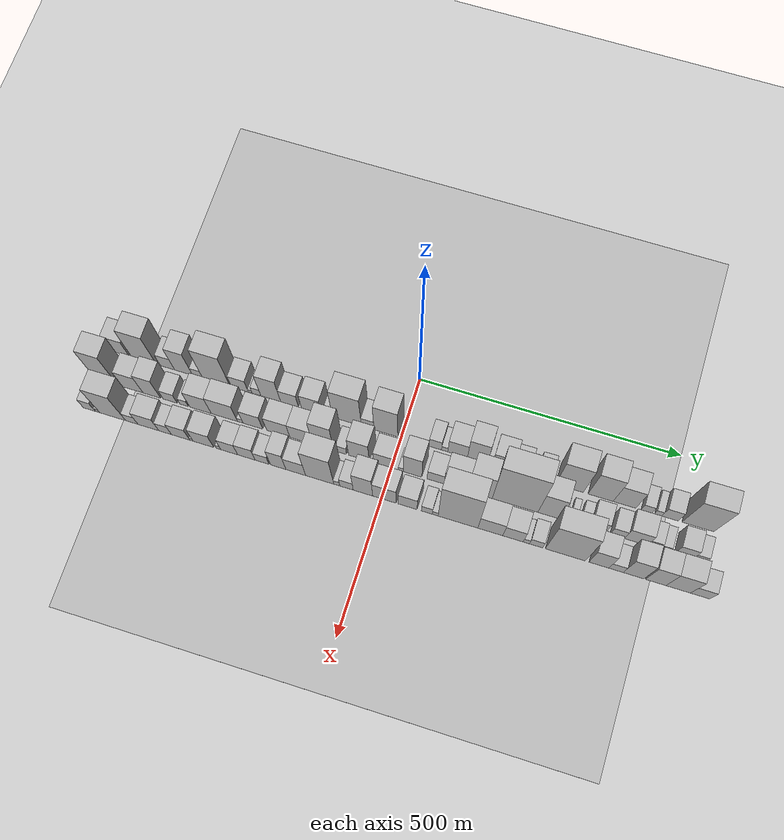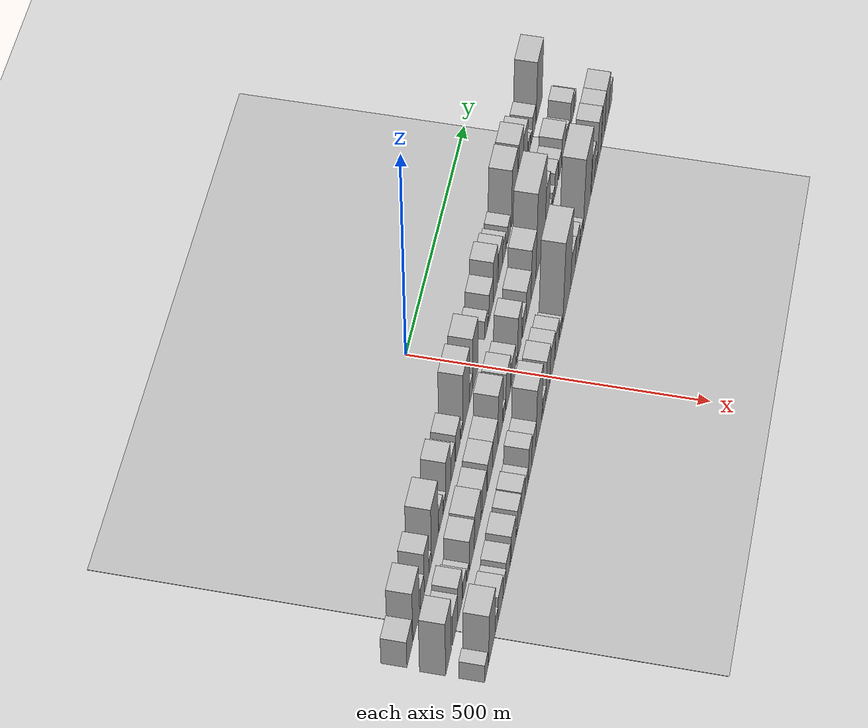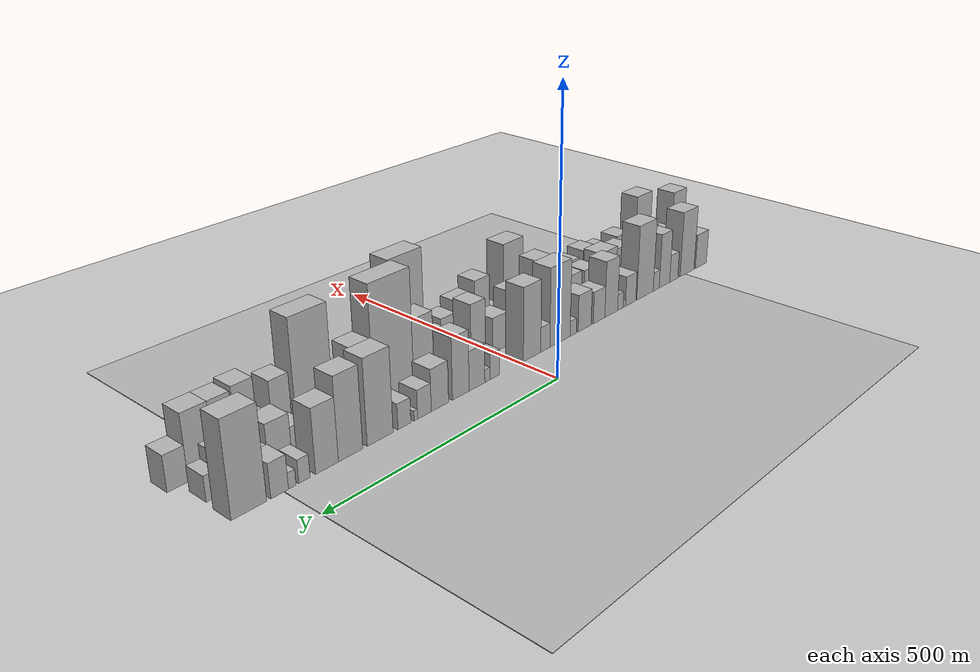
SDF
<?xml version="1.0" encoding="utf-8"?>

<sdf version="1.6">

   <world name="default">

      <gui fullscreen="0">

         <camera name="user_camera">

            <pose>-15 0 4.57585 0 0 0</pose>

            <view_controller>orbit</view_controller>

         </camera>

      </gui>

      <scene>

         <sky>

           <clouds>

             <speed>12</speed>

           </clouds>

         </sky>

         <ambient>0.4 0.4 0.4 1</ambient>

         <background>0.7 0.7 0.7 1</background>

         <shadows>1</shadows>

      </scene>

      <gravity>0 0 -9.8066</gravity>

      <magnetic_field>6e-06 2.3e-05 -4.2e-05</magnetic_field>

      <physics default="0" name="default_physics" type="ode">

         <ode>

            <solver>

               <type>quick</type>

               <iters>10</iters>

               <sor>1.0</sor>

               <use_dynamic_moi_rescaling>0</use_dynamic_moi_rescaling>

            </solver>

            <constraints>

               <cfm>0</cfm>

               <erp>0.2</erp>

               <contact_max_correcting_vel>100</contact_max_correcting_vel>

               <contact_surface_layer>0.001</contact_surface_layer>

            </constraints>

         </ode>

         <max_step_size>0.004</max_step_size>

         <real_time_factor>1</real_time_factor>

         <real_time_update_rate>250</real_time_update_rate>

      </physics>

      <light name="sun" type="directional">

         <cast_shadows>1</cast_shadows>

         <pose>0 0 10 0 0 0</pose>

         <diffuse>0.8 0.8 0.8 1</diffuse>

         <specular>0.2 0.2 0.2 1</specular>

         <attenuation>

            <range>1000</range>

            <constant>0.9</constant>

            <linear>0.01</linear>

            <quadratic>0.001</quadratic>

         </attenuation>

         <direction>-0.5 0.1 -0.9</direction>

      </light>

      <include>

         <name>ground_plane_1</name>

         <uri>model://HANNAS_ground_plane</uri>

         <pose>0 0 0  0 0 0</pose>

      </include>

      <include>

         <name>ground_plane_2</name>

         <uri>model://HANNAS_ground_plane</uri>

         <pose>100 0 0  0 0 0</pose>

      </include>

      <model name="building_1">

         <static>1</static>

         <pose frame="">100.0000 -556.5266 0 0.000000 0.000000 0.000000</pose>

         <link name="link">

            <pose frame="">0 0 36.00 0 0 0</pose>

            <collision name="collision">

               <geometry>

                  <box>

                     <size>40.0000 40.9467 72.0000</size>

                  </box>

               </geometry>

               <max_contacts>10</max_contacts>

               <surface>

                  <contact>

                     <ode/>

                  </contact>

                  <bounce/>

                  <friction>

                     <torsional>

                        <ode/>

                     </torsional>

                     <ode/>

                  </friction>

               </surface>

            </collision>

            <visual name="visual">

               <cast_shadows>0</cast_shadows>

               <geometry>

                  <box>

                     <size>40.0000 40.9467 72.0000</size>

                  </box>

               </geometry>

               <material>

                  <script>

                     <uri>model://HANNAS_wall/materials/scripts</uri>

                     <uri>model://HANNAS_wall/materials/textures</uri>

                     <name>vrc/HANNAS_wall</name>

                  </script>

               </material>

            </visual>

            <self_collide>0</self_collide>

            <enable_wind>0</enable_wind>

            <kinematic>0</kinematic>

         </link>

      </model>

      <model name="building_2">

         <static>1</static>

         <pose frame="">100.0000 -506.0978 0 0.000000 0.000000 0.000000</pose>

         <link name="link">

            <pose frame="">0 0 67.50 0 0 0</pose>

            <collision name="collision">

               <geometry>

                  <box>

                     <size>40.0000 49.9109 135.0000</size>

                  </box>

               </geometry>

               <max_contacts>10</max_contacts>

               <surface>

                  <contact>

                     <ode/>

                  </contact>

                  <bounce/>

                  <friction>

                     <torsional>

                        <ode/>

                     </torsional>

                     <ode/>

                  </friction>

               </surface>

            </collision>

            <visual name="visual">

               <cast_shadows>0</cast_shadows>

               <geometry>

                  <box>

                     <size>40.0000 49.9109 135.0000</size>

                  </box>

               </geometry>

               <material>

                  <script>

                     <uri>model://HANNAS_wall/materials/scripts</uri>

                     <uri>model://HANNAS_wall/materials/textures</uri>

                     <name>vrc/HANNAS_wall</name>

                  </script>

               </material>

            </visual>

            <self_collide>0</self_collide>

            <enable_wind>0</enable_wind>

            <kinematic>0</kinematic>

         </link>

      </model>

      <model name="building_3">

         <static>1</static>

         <pose frame="">100.0000 -458.8349 0 0.000000 0.000000 0.000000</pose>

         <link name="link">

            <pose frame="">0 0 28.50 0 0 0</pose>

            <collision name="collision">

               <geometry>

                  <box>

                     <size>40.0000 28.6148 57.0000</size>

                  </box>

               </geometry>

               <max_contacts>10</max_contacts>

               <surface>

                  <contact>

                     <ode/>

                  </contact>

                  <bounce/>

                  <friction>

                     <torsional>

                        <ode/>

                     </torsional>

                     <ode/>

                  </friction>

               </surface>

            </collision>

            <visual name="visual">

               <cast_shadows>0</cast_shadows>

               <geometry>

                  <box>

                     <size>40.0000 28.6148 57.0000</size>

                  </box>

               </geometry>

               <material>

                  <script>

                     <uri>model://HANNAS_wall/materials/scripts</uri>

                     <uri>model://HANNAS_wall/materials/textures</uri>

                     <name>vrc/HANNAS_wall</name>

                  </script>

               </material>

            </visual>

            <self_collide>0</self_collide>

            <enable_wind>0</enable_wind>

            <kinematic>0</kinematic>

         </link>

      </model>

      <model name="building_4">

         <static>1</static>

         <pose frame="">100.0000 -426.6664 0 0.000000 0.000000 0.000000</pose>

         <link name="link">

            <pose frame="">0 0 55.50 0 0 0</pose>

            <collision name="collision">

               <geometry>

                  <box>

                     <size>40.0000 35.7224 111.0000</size>

                  </box>

               </geometry>

               <max_contacts>10</max_contacts>

               <surface>

                  <contact>

                     <ode/>

                  </contact>

                  <bounce/>

                  <friction>

                     <torsional>

                        <ode/>

                     </torsional>

                     <ode/>

                  </friction>

               </surface>

            </collision>

            <visual name="visual">

               <cast_shadows>0</cast_shadows>

               <geometry>

                  <box>

                     <size>40.0000 35.7224 111.0000</size>

                  </box>

               </geometry>

               <material>

                  <script>

                     <uri>model://HANNAS_wall/materials/scripts</uri>

                     <uri>model://HANNAS_wall/materials/textures</uri>

                     <name>vrc/HANNAS_wall</name>

                  </script>

               </material>

            </visual>

            <self_collide>0</self_collide>

            <enable_wind>0</enable_wind>

            <kinematic>0</kinematic>

         </link>

      </model>

      <model name="building_5">

         <static>1</static>

         <pose frame="">100.0000 -398.7669 0 0.000000 0.000000 0.000000</pose>

         <link name="link">

            <pose frame="">0 0 19.50 0 0 0</pose>

            <collision name="collision">

               <geometry>

                  <box>

                     <size>40.0000 20.0766 39.0000</size>

                  </box>

               </geometry>

               <max_contacts>10</max_contacts>

               <surface>

                  <contact>

                     <ode/>

                  </contact>

                  <bounce/>

                  <friction>

                     <torsional>

                        <ode/>

                     </torsional>

                     <ode/>

                  </friction>

               </surface>

            </collision>

            <visual name="visual">

               <cast_shadows>0</cast_shadows>

               <geometry>

                  <box>

                     <size>40.0000 20.0766 39.0000</size>

                  </box>

               </geometry>

               <material>

                  <script>

                     <uri>model://HANNAS_wall/materials/scripts</uri>

                     <uri>model://HANNAS_wall/materials/textures</uri>

                     <name>vrc/HANNAS_wall</name>

                  </script>

               </material>

            </visual>

            <self_collide>0</self_collide>

            <enable_wind>0</enable_wind>

            <kinematic>0</kinematic>

         </link>

      </model>

      <model name="building_6">

         <static>1</static>

         <pose frame="">100.0000 -361.5267 0 0.000000 0.000000 0.000000</pose>

         <link name="link">

            <pose frame="">0 0 75.00 0 0 0</pose>

            <collision name="collision">

               <geometry>

                  <box>

                     <size>40.0000 54.4038 150.0000</size>

                  </box>

               </geometry>

               <max_contacts>10</max_contacts>

               <surface>

                  <contact>

                     <ode/>

                  </contact>

                  <bounce/>

                  <friction>

                     <torsional>

                        <ode/>

                     </torsional>

                     <ode/>

                  </friction>

               </surface>

            </collision>

            <visual name="visual">

               <cast_shadows>0</cast_shadows>

               <geometry>

                  <box>

                     <size>40.0000 54.4038 150.0000</size>

                  </box>

               </geometry>

               <material>

                  <script>

                     <uri>model://HANNAS_wall/materials/scripts</uri>

                     <uri>model://HANNAS_wall/materials/textures</uri>

                     <name>vrc/HANNAS_wall</name>

                  </script>

               </material>

            </visual>

            <self_collide>0</self_collide>

            <enable_wind>0</enable_wind>

            <kinematic>0</kinematic>

         </link>

      </model>

      <model name="building_7">

         <static>1</static>

         <pose frame="">100.0000 -314.9015 0 0.000000 0.000000 0.000000</pose>

         <link name="link">

            <pose frame="">0 0 30.00 0 0 0</pose>

            <collision name="collision">

               <geometry>

                  <box>

                     <size>40.0000 32.8466 60.0000</size>

                  </box>

               </geometry>

               <max_contacts>10</max_contacts>

               <surface>

                  <contact>

                     <ode/>

                  </contact>

                  <bounce/>

                  <friction>

                     <torsional>

                        <ode/>

                     </torsional>

                     <ode/>

                  </friction>

               </surface>

            </collision>

            <visual name="visual">

               <cast_shadows>0</cast_shadows>

               <geometry>

                  <box>

                     <size>40.0000 32.8466 60.0000</size>

                  </box>

               </geometry>

               <material>

                  <script>

                     <uri>model://HANNAS_wall/materials/scripts</uri>

                     <uri>model://HANNAS_wall/materials/textures</uri>

                     <name>vrc/HANNAS_wall</name>

                  </script>

               </material>

            </visual>

            <self_collide>0</self_collide>

            <enable_wind>0</enable_wind>

            <kinematic>0</kinematic>

         </link>

      </model>

      <model name="building_8">

         <static>1</static>

         <pose frame="">100.0000 -294.7774 0 0.000000 0.000000 0.000000</pose>

         <link name="link">

            <pose frame="">0 0 7.50 0 0 0</pose>

            <collision name="collision">

               <geometry>

                  <box>

                     <size>40.0000 7.4018 15.0000</size>

                  </box>

               </geometry>

               <max_contacts>10</max_contacts>

               <surface>

                  <contact>

                     <ode/>

                  </contact>

                  <bounce/>

                  <friction>

                     <torsional>

                        <ode/>

                     </torsional>

                     <ode/>

                  </friction>

               </surface>

            </collision>

            <visual name="visual">

               <cast_shadows>0</cast_shadows>

               <geometry>

                  <box>

                     <size>40.0000 7.4018 15.0000</size>

                  </box>

               </geometry>

               <material>

                  <script>

                     <uri>model://HANNAS_wall/materials/scripts</uri>

                     <uri>model://HANNAS_wall/materials/textures</uri>

                     <name>vrc/HANNAS_wall</name>

                  </script>

               </material>

            </visual>

            <self_collide>0</self_collide>

            <enable_wind>0</enable_wind>

            <kinematic>0</kinematic>

         </link>

      </model>

      <model name="building_9">

         <static>1</static>

         <pose frame="">100.0000 -282.3740 0 0.000000 0.000000 0.000000</pose>

         <link name="link">

            <pose frame="">0 0 16.50 0 0 0</pose>

            <collision name="collision">

               <geometry>

                  <box>

                     <size>40.0000 17.4050 33.0000</size>

                  </box>

               </geometry>

               <max_contacts>10</max_contacts>

               <surface>

                  <contact>

                     <ode/>

                  </contact>

                  <bounce/>

                  <friction>

                     <torsional>

                        <ode/>

                     </torsional>

                     <ode/>

                  </friction>

               </surface>

            </collision>

            <visual name="visual">

               <cast_shadows>0</cast_shadows>

               <geometry>

                  <box>

                     <size>40.0000 17.4050 33.0000</size>

                  </box>

               </geometry>

               <material>

                  <script>

                     <uri>model://HANNAS_wall/materials/scripts</uri>

                     <uri>model://HANNAS_wall/materials/textures</uri>

                     <name>vrc/HANNAS_wall</name>

                  </script>

               </material>

            </visual>

            <self_collide>0</self_collide>

            <enable_wind>0</enable_wind>

            <kinematic>0</kinematic>

         </link>

      </model>

      <model name="building_10">

         <static>1</static>

         <pose frame="">100.0000 -254.1401 0 0.000000 0.000000 0.000000</pose>

         <link name="link">

            <pose frame="">0 0 55.50 0 0 0</pose>

            <collision name="collision">

               <geometry>

                  <box>

                     <size>40.0000 39.0629 111.0000</size>

                  </box>

               </geometry>

               <max_contacts>10</max_contacts>

               <surface>

                  <contact>

                     <ode/>

                  </contact>

                  <bounce/>

                  <friction>

                     <torsional>

                        <ode/>

                     </torsional>

                     <ode/>

                  </friction>

               </surface>

            </collision>

            <visual name="visual">

               <cast_shadows>0</cast_shadows>

               <geometry>

                  <box>

                     <size>40.0000 39.0629 111.0000</size>

                  </box>

               </geometry>

               <material>

                  <script>

                     <uri>model://HANNAS_wall/materials/scripts</uri>

                     <uri>model://HANNAS_wall/materials/textures</uri>

                     <name>vrc/HANNAS_wall</name>

                  </script>

               </material>

            </visual>

            <self_collide>0</self_collide>

            <enable_wind>0</enable_wind>

            <kinematic>0</kinematic>

         </link>

      </model>

      <model name="building_11">

         <static>1</static>

         <pose frame="">100.0000 -217.1890 0 0.000000 0.000000 0.000000</pose>

         <link name="link">

            <pose frame="">0 0 31.50 0 0 0</pose>

            <collision name="collision">

               <geometry>

                  <box>

                     <size>40.0000 34.8394 63.0000</size>

                  </box>

               </geometry>

               <max_contacts>10</max_contacts>

               <surface>

                  <contact>

                     <ode/>

                  </contact>

                  <bounce/>

                  <friction>

                     <torsional>

                        <ode/>

                     </torsional>

                     <ode/>

                  </friction>

               </surface>

            </collision>

            <visual name="visual">

               <cast_shadows>0</cast_shadows>

               <geometry>

                  <box>

                     <size>40.0000 34.8394 63.0000</size>

                  </box>

               </geometry>

               <material>

                  <script>

                     <uri>model://HANNAS_wall/materials/scripts</uri>

                     <uri>model://HANNAS_wall/materials/textures</uri>

                     <name>vrc/HANNAS_wall</name>

                  </script>

               </material>

            </visual>

            <self_collide>0</self_collide>

            <enable_wind>0</enable_wind>

            <kinematic>0</kinematic>

         </link>

      </model>

      <model name="building_12">

         <static>1</static>

         <pose frame="">100.0000 -174.7387 0 0.000000 0.000000 0.000000</pose>

         <link name="link">

            <pose frame="">0 0 36.00 0 0 0</pose>

            <collision name="collision">

               <geometry>

                  <box>

                     <size>40.0000 38.0611 72.0000</size>

                  </box>

               </geometry>

               <max_contacts>10</max_contacts>

               <surface>

                  <contact>

                     <ode/>

                  </contact>

                  <bounce/>

                  <friction>

                     <torsional>

                        <ode/>

                     </torsional>

                     <ode/>

                  </friction>

               </surface>

            </collision>

            <visual name="visual">

               <cast_shadows>0</cast_shadows>

               <geometry>

                  <box>

                     <size>40.0000 38.0611 72.0000</size>

                  </box>

               </geometry>

               <material>

                  <script>

                     <uri>model://HANNAS_wall/materials/scripts</uri>

                     <uri>model://HANNAS_wall/materials/textures</uri>

                     <name>vrc/HANNAS_wall</name>

                  </script>

               </material>

            </visual>

            <self_collide>0</self_collide>

            <enable_wind>0</enable_wind>

            <kinematic>0</kinematic>

         </link>

      </model>

      <model name="building_13">

         <static>1</static>

         <pose frame="">100.0000 -141.8190 0 0.000000 0.000000 0.000000</pose>

         <link name="link">

            <pose frame="">0 0 15.00 0 0 0</pose>

            <collision name="collision">

               <geometry>

                  <box>

                     <size>40.0000 17.7782 30.0000</size>

                  </box>

               </geometry>

               <max_contacts>10</max_contacts>

               <surface>

                  <contact>

                     <ode/>

                  </contact>

                  <bounce/>

                  <friction>

                     <torsional>

                        <ode/>

                     </torsional>

                     <ode/>

                  </friction>

               </surface>

            </collision>

            <visual name="visual">

               <cast_shadows>0</cast_shadows>

               <geometry>

                  <box>

                     <size>40.0000 17.7782 30.0000</size>

                  </box>

               </geometry>

               <material>

                  <script>

                     <uri>model://HANNAS_wall/materials/scripts</uri>

                     <uri>model://HANNAS_wall/materials/textures</uri>

                     <name>vrc/HANNAS_wall</name>

                  </script>

               </material>

            </visual>

            <self_collide>0</self_collide>

            <enable_wind>0</enable_wind>

            <kinematic>0</kinematic>

         </link>

      </model>

      <model name="building_14">

         <static>1</static>

         <pose frame="">100.0000 -104.8414 0 0.000000 0.000000 0.000000</pose>

         <link name="link">

            <pose frame="">0 0 75.00 0 0 0</pose>

            <collision name="collision">

               <geometry>

                  <box>

                     <size>40.0000 56.1771 150.0000</size>

                  </box>

               </geometry>

               <max_contacts>10</max_contacts>

               <surface>

                  <contact>

                     <ode/>

                  </contact>

                  <bounce/>

                  <friction>

                     <torsional>

                        <ode/>

                     </torsional>

                     <ode/>

                  </friction>

               </surface>

            </collision>

            <visual name="visual">

               <cast_shadows>0</cast_shadows>

               <geometry>

                  <box>

                     <size>40.0000 56.1771 150.0000</size>

                  </box>

               </geometry>

               <material>

                  <script>

                     <uri>model://HANNAS_wall/materials/scripts</uri>

                     <uri>model://HANNAS_wall/materials/textures</uri>

                     <name>vrc/HANNAS_wall</name>

                  </script>

               </material>

            </visual>

            <self_collide>0</self_collide>

            <enable_wind>0</enable_wind>

            <kinematic>0</kinematic>

         </link>

      </model>

      <model name="building_15">

         <static>1</static>

         <pose frame="">100.0000 -64.5177 0 0.000000 0.000000 0.000000</pose>

         <link name="link">

            <pose frame="">0 0 24.00 0 0 0</pose>

            <collision name="collision">

               <geometry>

                  <box>

                     <size>40.0000 24.4703 48.0000</size>

                  </box>

               </geometry>

               <max_contacts>10</max_contacts>

               <surface>

                  <contact>

                     <ode/>

                  </contact>

                  <bounce/>

                  <friction>

                     <torsional>

                        <ode/>

                     </torsional>

                     <ode/>

                  </friction>

               </surface>

            </collision>

            <visual name="visual">

               <cast_shadows>0</cast_shadows>

               <geometry>

                  <box>

                     <size>40.0000 24.4703 48.0000</size>

                  </box>

               </geometry>

               <material>

                  <script>

                     <uri>model://HANNAS_wall/materials/scripts</uri>

                     <uri>model://HANNAS_wall/materials/textures</uri>

                     <name>vrc/HANNAS_wall</name>

                  </script>

               </material>

            </visual>

            <self_collide>0</self_collide>

            <enable_wind>0</enable_wind>

            <kinematic>0</kinematic>

         </link>

      </model>

      <model name="building_16">

         <static>1</static>

         <pose frame="">100.0000 -29.4115 0 0.000000 0.000000 0.000000</pose>

         <link name="link">

            <pose frame="">0 0 69.00 0 0 0</pose>

            <collision name="collision">

               <geometry>

                  <box>

                     <size>40.0000 45.7420 138.0000</size>

                  </box>

               </geometry>

               <max_contacts>10</max_contacts>

               <surface>

                  <contact>

                     <ode/>

                  </contact>

                  <bounce/>

                  <friction>

                     <torsional>

                        <ode/>

                     </torsional>

                     <ode/>

                  </friction>

               </surface>

            </collision>

            <visual name="visual">

               <cast_shadows>0</cast_shadows>

               <geometry>

                  <box>

                     <size>40.0000 45.7420 138.0000</size>

                  </box>

               </geometry>

               <material>

                  <script>

                     <uri>model://HANNAS_wall/materials/scripts</uri>

                     <uri>model://HANNAS_wall/materials/textures</uri>

                     <name>vrc/HANNAS_wall</name>

                  </script>

               </material>

            </visual>

            <self_collide>0</self_collide>

            <enable_wind>0</enable_wind>

            <kinematic>0</kinematic>

         </link>

      </model>

      <model name="building_17">

         <static>1</static>

         <pose frame="">100.0000 65.5070 0 0.000000 0.000000 0.000000</pose>

         <link name="link">

            <pose frame="">0 0 24.00 0 0 0</pose>

            <collision name="collision">

               <geometry>

                  <box>

                     <size>40.0000 24.0317 48.0000</size>

                  </box>

               </geometry>

               <max_contacts>10</max_contacts>

               <surface>

                  <contact>

                     <ode/>

                  </contact>

                  <bounce/>

                  <friction>

                     <torsional>

                        <ode/>

                     </torsional>

                     <ode/>

                  </friction>

               </surface>

            </collision>

            <visual name="visual">

               <cast_shadows>0</cast_shadows>

               <geometry>

                  <box>

                     <size>40.0000 24.0317 48.0000</size>

                  </box>

               </geometry>

               <material>

                  <script>

                     <uri>model://HANNAS_wall/materials/scripts</uri>

                     <uri>model://HANNAS_wall/materials/textures</uri>

                     <name>vrc/HANNAS_wall</name>

                  </script>

               </material>

            </visual>

            <self_collide>0</self_collide>

            <enable_wind>0</enable_wind>

            <kinematic>0</kinematic>

         </link>

      </model>

      <model name="building_18">

         <static>1</static>

         <pose frame="">100.0000 83.5056 0 0.000000 0.000000 0.000000</pose>

         <link name="link">

            <pose frame="">0 0 12.00 0 0 0</pose>

            <collision name="collision">

               <geometry>

                  <box>

                     <size>40.0000 11.9656 24.0000</size>

                  </box>

               </geometry>

               <max_contacts>10</max_contacts>

               <surface>

                  <contact>

                     <ode/>

                  </contact>

                  <bounce/>

                  <friction>

                     <torsional>

                        <ode/>

                     </torsional>

                     <ode/>

                  </friction>

               </surface>

            </collision>

            <visual name="visual">

               <cast_shadows>0</cast_shadows>

               <geometry>

                  <box>

                     <size>40.0000 11.9656 24.0000</size>

                  </box>

               </geometry>

               <material>

                  <script>

                     <uri>model://HANNAS_wall/materials/scripts</uri>

                     <uri>model://HANNAS_wall/materials/textures</uri>

                     <name>vrc/HANNAS_wall</name>

                  </script>

               </material>

            </visual>

            <self_collide>0</self_collide>

            <enable_wind>0</enable_wind>

            <kinematic>0</kinematic>

         </link>

      </model>

      <model name="building_19">

         <static>1</static>

         <pose frame="">100.0000 108.2624 0 0.000000 0.000000 0.000000</pose>

         <link name="link">

            <pose frame="">0 0 36.00 0 0 0</pose>

            <collision name="collision">

               <geometry>

                  <box>

                     <size>40.0000 37.5479 72.0000</size>

                  </box>

               </geometry>

               <max_contacts>10</max_contacts>

               <surface>

                  <contact>

                     <ode/>

                  </contact>

                  <bounce/>

                  <friction>

                     <torsional>

                        <ode/>

                     </torsional>

                     <ode/>

                  </friction>

               </surface>

            </collision>

            <visual name="visual">

               <cast_shadows>0</cast_shadows>

               <geometry>

                  <box>

                     <size>40.0000 37.5479 72.0000</size>

                  </box>

               </geometry>

               <material>

                  <script>

                     <uri>model://HANNAS_wall/materials/scripts</uri>

                     <uri>model://HANNAS_wall/materials/textures</uri>

                     <name>vrc/HANNAS_wall</name>

                  </script>

               </material>

            </visual>

            <self_collide>0</self_collide>

            <enable_wind>0</enable_wind>

            <kinematic>0</kinematic>

         </link>

      </model>

      <model name="building_20">

         <static>1</static>

         <pose frame="">100.0000 146.2265 0 0.000000 0.000000 0.000000</pose>

         <link name="link">

            <pose frame="">0 0 55.50 0 0 0</pose>

            <collision name="collision">

               <geometry>

                  <box>

                     <size>40.0000 38.3804 111.0000</size>

                  </box>

               </geometry>

               <max_contacts>10</max_contacts>

               <surface>

                  <contact>

                     <ode/>

                  </contact>

                  <bounce/>

                  <friction>

                     <torsional>

                        <ode/>

                     </torsional>

                     <ode/>

                  </friction>

               </surface>

            </collision>

            <visual name="visual">

               <cast_shadows>0</cast_shadows>

               <geometry>

                  <box>

                     <size>40.0000 38.3804 111.0000</size>

                  </box>

               </geometry>

               <material>

                  <script>

                     <uri>model://HANNAS_wall/materials/scripts</uri>

                     <uri>model://HANNAS_wall/materials/textures</uri>

                     <name>vrc/HANNAS_wall</name>

                  </script>

               </material>

            </visual>

            <self_collide>0</self_collide>

            <enable_wind>0</enable_wind>

            <kinematic>0</kinematic>

         </link>

      </model>

      <model name="building_21">

         <static>1</static>

         <pose frame="">100.0000 193.6616 0 0.000000 0.000000 0.000000</pose>

         <link name="link">

            <pose frame="">0 0 37.50 0 0 0</pose>

            <collision name="collision">

               <geometry>

                  <box>

                     <size>40.0000 38.4899 75.0000</size>

                  </box>

               </geometry>

               <max_contacts>10</max_contacts>

               <surface>

                  <contact>

                     <ode/>

                  </contact>

                  <bounce/>

                  <friction>

                     <torsional>

                        <ode/>

                     </torsional>

                     <ode/>

                  </friction>

               </surface>

            </collision>

            <visual name="visual">

               <cast_shadows>0</cast_shadows>

               <geometry>

                  <box>

                     <size>40.0000 38.4899 75.0000</size>

                  </box>

               </geometry>

               <material>

                  <script>

                     <uri>model://HANNAS_wall/materials/scripts</uri>

                     <uri>model://HANNAS_wall/materials/textures</uri>

                     <name>vrc/HANNAS_wall</name>

                  </script>

               </material>

            </visual>

            <self_collide>0</self_collide>

            <enable_wind>0</enable_wind>

            <kinematic>0</kinematic>

         </link>

      </model>

      <model name="building_22">

         <static>1</static>

         <pose frame="">100.0000 227.7586 0 0.000000 0.000000 0.000000</pose>

         <link name="link">

            <pose frame="">0 0 25.50 0 0 0</pose>

            <collision name="collision">

               <geometry>

                  <box>

                     <size>40.0000 29.7039 51.0000</size>

                  </box>

               </geometry>

               <max_contacts>10</max_contacts>

               <surface>

                  <contact>

                     <ode/>

                  </contact>

                  <bounce/>

                  <friction>

                     <torsional>

                        <ode/>

                     </torsional>

                     <ode/>

                  </friction>

               </surface>

            </collision>

            <visual name="visual">

               <cast_shadows>0</cast_shadows>

               <geometry>

                  <box>

                     <size>40.0000 29.7039 51.0000</size>

                  </box>

               </geometry>

               <material>

                  <script>

                     <uri>model://HANNAS_wall/materials/scripts</uri>

                     <uri>model://HANNAS_wall/materials/textures</uri>

                     <name>vrc/HANNAS_wall</name>

                  </script>

               </material>

            </visual>

            <self_collide>0</self_collide>

            <enable_wind>0</enable_wind>

            <kinematic>0</kinematic>

         </link>

      </model>

      <model name="building_23">

         <static>1</static>

         <pose frame="">100.0000 246.4136 0 0.000000 0.000000 0.000000</pose>

         <link name="link">

            <pose frame="">0 0 9.00 0 0 0</pose>

            <collision name="collision">

               <geometry>

                  <box>

                     <size>40.0000 7.6060 18.0000</size>

                  </box>

               </geometry>

               <max_contacts>10</max_contacts>

               <surface>

                  <contact>

                     <ode/>

                  </contact>

                  <bounce/>

                  <friction>

                     <torsional>

                        <ode/>

                     </torsional>

                     <ode/>

                  </friction>

               </surface>

            </collision>

            <visual name="visual">

               <cast_shadows>0</cast_shadows>

               <geometry>

                  <box>

                     <size>40.0000 7.6060 18.0000</size>

                  </box>

               </geometry>

               <material>

                  <script>

                     <uri>model://HANNAS_wall/materials/scripts</uri>

                     <uri>model://HANNAS_wall/materials/textures</uri>

                     <name>vrc/HANNAS_wall</name>

                  </script>

               </material>

            </visual>

            <self_collide>0</self_collide>

            <enable_wind>0</enable_wind>

            <kinematic>0</kinematic>

         </link>

      </model>

      <model name="building_24">

         <static>1</static>

         <pose frame="">100.0000 270.6468 0 0.000000 0.000000 0.000000</pose>

         <link name="link">

            <pose frame="">0 0 22.50 0 0 0</pose>

            <collision name="collision">

               <geometry>

                  <box>

                     <size>40.0000 26.8606 45.0000</size>

                  </box>

               </geometry>

               <max_contacts>10</max_contacts>

               <surface>

                  <contact>

                     <ode/>

                  </contact>

                  <bounce/>

                  <friction>

                     <torsional>

                        <ode/>

                     </torsional>

                     <ode/>

                  </friction>

               </surface>

            </collision>

            <visual name="visual">

               <cast_shadows>0</cast_shadows>

               <geometry>

                  <box>

                     <size>40.0000 26.8606 45.0000</size>

                  </box>

               </geometry>

               <material>

                  <script>

                     <uri>model://HANNAS_wall/materials/scripts</uri>

                     <uri>model://HANNAS_wall/materials/textures</uri>

                     <name>vrc/HANNAS_wall</name>

                  </script>

               </material>

            </visual>

            <self_collide>0</self_collide>

            <enable_wind>0</enable_wind>

            <kinematic>0</kinematic>

         </link>

      </model>

      <model name="building_25">

         <static>1</static>

         <pose frame="">100.0000 320.1162 0 0.000000 0.000000 0.000000</pose>

         <link name="link">

            <pose frame="">0 0 73.50 0 0 0</pose>

            <collision name="collision">

               <geometry>

                  <box>

                     <size>40.0000 52.0781 147.0000</size>

                  </box>

               </geometry>

               <max_contacts>10</max_contacts>

               <surface>

                  <contact>

                     <ode/>

                  </contact>

                  <bounce/>

                  <friction>

                     <torsional>

                        <ode/>

                     </torsional>

                     <ode/>

                  </friction>

               </surface>

            </collision>

            <visual name="visual">

               <cast_shadows>0</cast_shadows>

               <geometry>

                  <box>

                     <size>40.0000 52.0781 147.0000</size>

                  </box>

               </geometry>

               <material>

                  <script>

                     <uri>model://HANNAS_wall/materials/scripts</uri>

                     <uri>model://HANNAS_wall/materials/textures</uri>

                     <name>vrc/HANNAS_wall</name>

                  </script>

               </material>

            </visual>

            <self_collide>0</self_collide>

            <enable_wind>0</enable_wind>

            <kinematic>0</kinematic>

         </link>

      </model>

      <model name="building_26">

         <static>1</static>

         <pose frame="">100.0000 378.4985 0 0.000000 0.000000 0.000000</pose>

         <link name="link">

            <pose frame="">0 0 70.50 0 0 0</pose>

            <collision name="collision">

               <geometry>

                  <box>

                     <size>40.0000 46.6864 141.0000</size>

                  </box>

               </geometry>

               <max_contacts>10</max_contacts>

               <surface>

                  <contact>

                     <ode/>

                  </contact>

                  <bounce/>

                  <friction>

                     <torsional>

                        <ode/>

                     </torsional>

                     <ode/>

                  </friction>

               </surface>

            </collision>

            <visual name="visual">

               <cast_shadows>0</cast_shadows>

               <geometry>

                  <box>

                     <size>40.0000 46.6864 141.0000</size>

                  </box>

               </geometry>

               <material>

                  <script>

                     <uri>model://HANNAS_wall/materials/scripts</uri>

                     <uri>model://HANNAS_wall/materials/textures</uri>

                     <name>vrc/HANNAS_wall</name>

                  </script>

               </material>

            </visual>

            <self_collide>0</self_collide>

            <enable_wind>0</enable_wind>

            <kinematic>0</kinematic>

         </link>

      </model>

      <model name="building_27">

         <static>1</static>

         <pose frame="">100.0000 422.9503 0 0.000000 0.000000 0.000000</pose>

         <link name="link">

            <pose frame="">0 0 54.00 0 0 0</pose>

            <collision name="collision">

               <geometry>

                  <box>

                     <size>40.0000 42.2172 108.0000</size>

                  </box>

               </geometry>

               <max_contacts>10</max_contacts>

               <surface>

                  <contact>

                     <ode/>

                  </contact>

                  <bounce/>

                  <friction>

                     <torsional>

                        <ode/>

                     </torsional>

                     <ode/>

                  </friction>

               </surface>

            </collision>

            <visual name="visual">

               <cast_shadows>0</cast_shadows>

               <geometry>

                  <box>

                     <size>40.0000 42.2172 108.0000</size>

                  </box>

               </geometry>

               <material>

                  <script>

                     <uri>model://HANNAS_wall/materials/scripts</uri>

                     <uri>model://HANNAS_wall/materials/textures</uri>

                     <name>vrc/HANNAS_wall</name>

                  </script>

               </material>

            </visual>

            <self_collide>0</self_collide>

            <enable_wind>0</enable_wind>

            <kinematic>0</kinematic>

         </link>

      </model>

      <model name="building_28">

         <static>1</static>

         <pose frame="">100.0000 464.1605 0 0.000000 0.000000 0.000000</pose>

         <link name="link">

            <pose frame="">0 0 19.50 0 0 0</pose>

            <collision name="collision">

               <geometry>

                  <box>

                     <size>40.0000 20.2033 39.0000</size>

                  </box>

               </geometry>

               <max_contacts>10</max_contacts>

               <surface>

                  <contact>

                     <ode/>

                  </contact>

                  <bounce/>

                  <friction>

                     <torsional>

                        <ode/>

                     </torsional>

                     <ode/>

                  </friction>

               </surface>

            </collision>

            <visual name="visual">

               <cast_shadows>0</cast_shadows>

               <geometry>

                  <box>

                     <size>40.0000 20.2033 39.0000</size>

                  </box>

               </geometry>

               <material>

                  <script>

                     <uri>model://HANNAS_wall/materials/scripts</uri>

                     <uri>model://HANNAS_wall/materials/textures</uri>

                     <name>vrc/HANNAS_wall</name>

                  </script>

               </material>

            </visual>

            <self_collide>0</self_collide>

            <enable_wind>0</enable_wind>

            <kinematic>0</kinematic>

         </link>

      </model>

      <model name="building_29">

         <static>1</static>

         <pose frame="">100.0000 485.8208 0 0.000000 0.000000 0.000000</pose>

         <link name="link">

            <pose frame="">0 0 13.50 0 0 0</pose>

            <collision name="collision">

               <geometry>

                  <box>

                     <size>40.0000 13.1172 27.0000</size>

                  </box>

               </geometry>

               <max_contacts>10</max_contacts>

               <surface>

                  <contact>

                     <ode/>

                  </contact>

                  <bounce/>

                  <friction>

                     <torsional>

                        <ode/>

                     </torsional>

                     <ode/>

                  </friction>

               </surface>

            </collision>

            <visual name="visual">

               <cast_shadows>0</cast_shadows>

               <geometry>

                  <box>

                     <size>40.0000 13.1172 27.0000</size>

                  </box>

               </geometry>

               <material>

                  <script>

                     <uri>model://HANNAS_wall/materials/scripts</uri>

                     <uri>model://HANNAS_wall/materials/textures</uri>

                     <name>vrc/HANNAS_wall</name>

                  </script>

               </material>

            </visual>

            <self_collide>0</self_collide>

            <enable_wind>0</enable_wind>

            <kinematic>0</kinematic>

         </link>

      </model>

      <model name="building_30">

         <static>1</static>

         <pose frame="">100.0000 507.6301 0 0.000000 0.000000 0.000000</pose>

         <link name="link">

            <pose frame="">0 0 28.50 0 0 0</pose>

            <collision name="collision">

               <geometry>

                  <box>

                     <size>40.0000 30.5014 57.0000</size>

                  </box>

               </geometry>

               <max_contacts>10</max_contacts>

               <surface>

                  <contact>

                     <ode/>

                  </contact>

                  <bounce/>

                  <friction>

                     <torsional>

                        <ode/>

                     </torsional>

                     <ode/>

                  </friction>

               </surface>

            </collision>

            <visual name="visual">

               <cast_shadows>0</cast_shadows>

               <geometry>

                  <box>

                     <size>40.0000 30.5014 57.0000</size>

                  </box>

               </geometry>

               <material>

                  <script>

                     <uri>model://HANNAS_wall/materials/scripts</uri>

                     <uri>model://HANNAS_wall/materials/textures</uri>

                     <name>vrc/HANNAS_wall</name>

                  </script>

               </material>

            </visual>

            <self_collide>0</self_collide>

            <enable_wind>0</enable_wind>

            <kinematic>0</kinematic>

         </link>

      </model>

      <model name="building_31">

         <static>1</static>

         <pose frame="">100.0000 559.2843 0 0.000000 0.000000 0.000000</pose>

         <link name="link">

            <pose frame="">0 0 78.00 0 0 0</pose>

            <collision name="collision">

               <geometry>

                  <box>

                     <size>40.0000 58.8070 156.0000</size>

                  </box>

               </geometry>

               <max_contacts>10</max_contacts>

               <surface>

                  <contact>

                     <ode/>

                  </contact>

                  <bounce/>

                  <friction>

                     <torsional>

                        <ode/>

                     </torsional>

                     <ode/>

                  </friction>

               </surface>

            </collision>

            <visual name="visual">

               <cast_shadows>0</cast_shadows>

               <geometry>

                  <box>

                     <size>40.0000 58.8070 156.0000</size>

                  </box>

               </geometry>

               <material>

                  <script>

                     <uri>model://HANNAS_wall/materials/scripts</uri>

                     <uri>model://HANNAS_wall/materials/textures</uri>

                     <name>vrc/HANNAS_wall</name>

                  </script>

               </material>

            </visual>

            <self_collide>0</self_collide>

            <enable_wind>0</enable_wind>

            <kinematic>0</kinematic>

         </link>

      </model>

      <model name="building_32">

         <static>1</static>

         <pose frame="">160.0000 -557.7676 0 0.000000 0.000000 0.000000</pose>

         <link name="link">

            <pose frame="">0 0 73.50 0 0 0</pose>

            <collision name="collision">

               <geometry>

                  <box>

                     <size>40.0000 44.4647 147.0000</size>

                  </box>

               </geometry>

               <max_contacts>10</max_contacts>

               <surface>

                  <contact>

                     <ode/>

                  </contact>

                  <bounce/>

                  <friction>

                     <torsional>

                        <ode/>

                     </torsional>

                     <ode/>

                  </friction>

               </surface>

            </collision>

            <visual name="visual">

               <cast_shadows>0</cast_shadows>

               <geometry>

                  <box>

                     <size>40.0000 44.4647 147.0000</size>

                  </box>

               </geometry>

               <material>

                  <script>

                     <uri>model://HANNAS_wall/materials/scripts</uri>

                     <uri>model://HANNAS_wall/materials/textures</uri>

                     <name>vrc/HANNAS_wall</name>

                  </script>

               </material>

            </visual>

            <self_collide>0</self_collide>

            <enable_wind>0</enable_wind>

            <kinematic>0</kinematic>

         </link>

      </model>

      <model name="building_33">

         <static>1</static>

         <pose frame="">160.0000 -505.2529 0 0.000000 0.000000 0.000000</pose>

         <link name="link">

            <pose frame="">0 0 40.50 0 0 0</pose>

            <collision name="collision">

               <geometry>

                  <box>

                     <size>40.0000 40.5649 81.0000</size>

                  </box>

               </geometry>

               <max_contacts>10</max_contacts>

               <surface>

                  <contact>

                     <ode/>

                  </contact>

                  <bounce/>

                  <friction>

                     <torsional>

                        <ode/>

                     </torsional>

                     <ode/>

                  </friction>

               </surface>

            </collision>

            <visual name="visual">

               <cast_shadows>0</cast_shadows>

               <geometry>

                  <box>

                     <size>40.0000 40.5649 81.0000</size>

                  </box>

               </geometry>

               <material>

                  <script>

                     <uri>model://HANNAS_wall/materials/scripts</uri>

                     <uri>model://HANNAS_wall/materials/textures</uri>

                     <name>vrc/HANNAS_wall</name>

                  </script>

               </material>

            </visual>

            <self_collide>0</self_collide>

            <enable_wind>0</enable_wind>

            <kinematic>0</kinematic>

         </link>

      </model>

      <model name="building_34">

         <static>1</static>

         <pose frame="">160.0000 -467.3385 0 0.000000 0.000000 0.000000</pose>

         <link name="link">

            <pose frame="">0 0 48.00 0 0 0</pose>

            <collision name="collision">

               <geometry>

                  <box>

                     <size>40.0000 35.2639 96.0000</size>

                  </box>

               </geometry>

               <max_contacts>10</max_contacts>

               <surface>

                  <contact>

                     <ode/>

                  </contact>

                  <bounce/>

                  <friction>

                     <torsional>

                        <ode/>

                     </torsional>

                     <ode/>

                  </friction>

               </surface>

            </collision>

            <visual name="visual">

               <cast_shadows>0</cast_shadows>

               <geometry>

                  <box>

                     <size>40.0000 35.2639 96.0000</size>

                  </box>

               </geometry>

               <material>

                  <script>

                     <uri>model://HANNAS_wall/materials/scripts</uri>

                     <uri>model://HANNAS_wall/materials/textures</uri>

                     <name>vrc/HANNAS_wall</name>

                  </script>

               </material>

            </visual>

            <self_collide>0</self_collide>

            <enable_wind>0</enable_wind>

            <kinematic>0</kinematic>

         </link>

      </model>

      <model name="building_35">

         <static>1</static>

         <pose frame="">160.0000 -430.7589 0 0.000000 0.000000 0.000000</pose>

         <link name="link">

            <pose frame="">0 0 24.00 0 0 0</pose>

            <collision name="collision">

               <geometry>

                  <box>

                     <size>40.0000 27.8953 48.0000</size>

                  </box>

               </geometry>

               <max_contacts>10</max_contacts>

               <surface>

                  <contact>

                     <ode/>

                  </contact>

                  <bounce/>

                  <friction>

                     <torsional>

                        <ode/>

                     </torsional>

                     <ode/>

                  </friction>

               </surface>

            </collision>

            <visual name="visual">

               <cast_shadows>0</cast_shadows>

               <geometry>

                  <box>

                     <size>40.0000 27.8953 48.0000</size>

                  </box>

               </geometry>

               <material>

                  <script>

                     <uri>model://HANNAS_wall/materials/scripts</uri>

                     <uri>model://HANNAS_wall/materials/textures</uri>

                     <name>vrc/HANNAS_wall</name>

                  </script>

               </material>

            </visual>

            <self_collide>0</self_collide>

            <enable_wind>0</enable_wind>

            <kinematic>0</kinematic>

         </link>

      </model>

      <model name="building_36">

         <static>1</static>

         <pose frame="">160.0000 -403.3605 0 0.000000 0.000000 0.000000</pose>

         <link name="link">

            <pose frame="">0 0 15.00 0 0 0</pose>

            <collision name="collision">

               <geometry>

                  <box>

                     <size>40.0000 16.9014 30.0000</size>

                  </box>

               </geometry>

               <max_contacts>10</max_contacts>

               <surface>

                  <contact>

                     <ode/>

                  </contact>

                  <bounce/>

                  <friction>

                     <torsional>

                        <ode/>

                     </torsional>

                     <ode/>

                  </friction>

               </surface>

            </collision>

            <visual name="visual">

               <cast_shadows>0</cast_shadows>

               <geometry>

                  <box>

                     <size>40.0000 16.9014 30.0000</size>

                  </box>

               </geometry>

               <material>

                  <script>

                     <uri>model://HANNAS_wall/materials/scripts</uri>

                     <uri>model://HANNAS_wall/materials/textures</uri>

                     <name>vrc/HANNAS_wall</name>

                  </script>

               </material>

            </visual>

            <self_collide>0</self_collide>

            <enable_wind>0</enable_wind>

            <kinematic>0</kinematic>

         </link>

      </model>

      <model name="building_37">

         <static>1</static>

         <pose frame="">160.0000 -370.7486 0 0.000000 0.000000 0.000000</pose>

         <link name="link">

            <pose frame="">0 0 42.00 0 0 0</pose>

            <collision name="collision">

               <geometry>

                  <box>

                     <size>40.0000 42.3224 84.0000</size>

                  </box>

               </geometry>

               <max_contacts>10</max_contacts>

               <surface>

                  <contact>

                     <ode/>

                  </contact>

                  <bounce/>

                  <friction>

                     <torsional>

                        <ode/>

                     </torsional>

                     <ode/>

                  </friction>

               </surface>

            </collision>

            <visual name="visual">

               <cast_shadows>0</cast_shadows>

               <geometry>

                  <box>

                     <size>40.0000 42.3224 84.0000</size>

                  </box>

               </geometry>

               <material>

                  <script>

                     <uri>model://HANNAS_wall/materials/scripts</uri>

                     <uri>model://HANNAS_wall/materials/textures</uri>

                     <name>vrc/HANNAS_wall</name>

                  </script>

               </material>

            </visual>

            <self_collide>0</self_collide>

            <enable_wind>0</enable_wind>

            <kinematic>0</kinematic>

         </link>

      </model>

      <model name="building_38">

         <static>1</static>

         <pose frame="">160.0000 -323.6521 0 0.000000 0.000000 0.000000</pose>

         <link name="link">

            <pose frame="">0 0 45.00 0 0 0</pose>

            <collision name="collision">

               <geometry>

                  <box>

                     <size>40.0000 51.8707 90.0000</size>

                  </box>

               </geometry>

               <max_contacts>10</max_contacts>

               <surface>

                  <contact>

                     <ode/>

                  </contact>

                  <bounce/>

                  <friction>

                     <torsional>

                        <ode/>

                     </torsional>

                     <ode/>

                  </friction>

               </surface>

            </collision>

            <visual name="visual">

               <cast_shadows>0</cast_shadows>

               <geometry>

                  <box>

                     <size>40.0000 51.8707 90.0000</size>

                  </box>

               </geometry>

               <material>

                  <script>

                     <uri>model://HANNAS_wall/materials/scripts</uri>

                     <uri>model://HANNAS_wall/materials/textures</uri>

                     <name>vrc/HANNAS_wall</name>

                  </script>

               </material>

            </visual>

            <self_collide>0</self_collide>

            <enable_wind>0</enable_wind>

            <kinematic>0</kinematic>

         </link>

      </model>

      <model name="building_39">

         <static>1</static>

         <pose frame="">160.0000 -292.5558 0 0.000000 0.000000 0.000000</pose>

         <link name="link">

            <pose frame="">0 0 10.50 0 0 0</pose>

            <collision name="collision">

               <geometry>

                  <box>

                     <size>40.0000 10.3218 21.0000</size>

                  </box>

               </geometry>

               <max_contacts>10</max_contacts>

               <surface>

                  <contact>

                     <ode/>

                  </contact>

                  <bounce/>

                  <friction>

                     <torsional>

                        <ode/>

                     </torsional>

                     <ode/>

                  </friction>

               </surface>

            </collision>

            <visual name="visual">

               <cast_shadows>0</cast_shadows>

               <geometry>

                  <box>

                     <size>40.0000 10.3218 21.0000</size>

                  </box>

               </geometry>

               <material>

                  <script>

                     <uri>model://HANNAS_wall/materials/scripts</uri>

                     <uri>model://HANNAS_wall/materials/textures</uri>

                     <name>vrc/HANNAS_wall</name>

                  </script>

               </material>

            </visual>

            <self_collide>0</self_collide>

            <enable_wind>0</enable_wind>

            <kinematic>0</kinematic>

         </link>

      </model>

      <model name="building_40">

         <static>1</static>

         <pose frame="">160.0000 -268.0277 0 0.000000 0.000000 0.000000</pose>

         <link name="link">

            <pose frame="">0 0 36.00 0 0 0</pose>

            <collision name="collision">

               <geometry>

                  <box>

                     <size>40.0000 38.7344 72.0000</size>

                  </box>

               </geometry>

               <max_contacts>10</max_contacts>

               <surface>

                  <contact>

                     <ode/>

                  </contact>

                  <bounce/>

                  <friction>

                     <torsional>

                        <ode/>

                     </torsional>

                     <ode/>

                  </friction>

               </surface>

            </collision>

            <visual name="visual">

               <cast_shadows>0</cast_shadows>

               <geometry>

                  <box>

                     <size>40.0000 38.7344 72.0000</size>

                  </box>

               </geometry>

               <material>

                  <script>

                     <uri>model://HANNAS_wall/materials/scripts</uri>

                     <uri>model://HANNAS_wall/materials/textures</uri>

                     <name>vrc/HANNAS_wall</name>

                  </script>

               </material>

            </visual>

            <self_collide>0</self_collide>

            <enable_wind>0</enable_wind>

            <kinematic>0</kinematic>

         </link>

      </model>

      <model name="building_41">

         <static>1</static>

         <pose frame="">160.0000 -218.2094 0 0.000000 0.000000 0.000000</pose>

         <link name="link">

            <pose frame="">0 0 37.50 0 0 0</pose>

            <collision name="collision">

               <geometry>

                  <box>

                     <size>40.0000 44.9022 75.0000</size>

                  </box>

               </geometry>

               <max_contacts>10</max_contacts>

               <surface>

                  <contact>

                     <ode/>

                  </contact>

                  <bounce/>

                  <friction>

                     <torsional>

                        <ode/>

                     </torsional>

                     <ode/>

                  </friction>

               </surface>

            </collision>

            <visual name="visual">

               <cast_shadows>0</cast_shadows>

               <geometry>

                  <box>

                     <size>40.0000 44.9022 75.0000</size>

                  </box>

               </geometry>

               <material>

                  <script>

                     <uri>model://HANNAS_wall/materials/scripts</uri>

                     <uri>model://HANNAS_wall/materials/textures</uri>

                     <name>vrc/HANNAS_wall</name>

                  </script>

               </material>

            </visual>

            <self_collide>0</self_collide>

            <enable_wind>0</enable_wind>

            <kinematic>0</kinematic>

         </link>

      </model>

      <model name="building_42">

         <static>1</static>

         <pose frame="">160.0000 -173.7281 0 0.000000 0.000000 0.000000</pose>

         <link name="link">

            <pose frame="">0 0 37.50 0 0 0</pose>

            <collision name="collision">

               <geometry>

                  <box>

                     <size>40.0000 44.0604 75.0000</size>

                  </box>

               </geometry>

               <max_contacts>10</max_contacts>

               <surface>

                  <contact>

                     <ode/>

                  </contact>

                  <bounce/>

                  <friction>

                     <torsional>

                        <ode/>

                     </torsional>

                     <ode/>

                  </friction>

               </surface>

            </collision>

            <visual name="visual">

               <cast_shadows>0</cast_shadows>

               <geometry>

                  <box>

                     <size>40.0000 44.0604 75.0000</size>

                  </box>

               </geometry>

               <material>

                  <script>

                     <uri>model://HANNAS_wall/materials/scripts</uri>

                     <uri>model://HANNAS_wall/materials/textures</uri>

                     <name>vrc/HANNAS_wall</name>

                  </script>

               </material>

            </visual>

            <self_collide>0</self_collide>

            <enable_wind>0</enable_wind>

            <kinematic>0</kinematic>

         </link>

      </model>

      <model name="building_43">

         <static>1</static>

         <pose frame="">160.0000 -131.1166 0 0.000000 0.000000 0.000000</pose>

         <link name="link">

            <pose frame="">0 0 67.50 0 0 0</pose>

            <collision name="collision">

               <geometry>

                  <box>

                     <size>40.0000 41.1627 135.0000</size>

                  </box>

               </geometry>

               <max_contacts>10</max_contacts>

               <surface>

                  <contact>

                     <ode/>

                  </contact>

                  <bounce/>

                  <friction>

                     <torsional>

                        <ode/>

                     </torsional>

                     <ode/>

                  </friction>

               </surface>

            </collision>

            <visual name="visual">

               <cast_shadows>0</cast_shadows>

               <geometry>

                  <box>

                     <size>40.0000 41.1627 135.0000</size>

                  </box>

               </geometry>

               <material>

                  <script>

                     <uri>model://HANNAS_wall/materials/scripts</uri>

                     <uri>model://HANNAS_wall/materials/textures</uri>

                     <name>vrc/HANNAS_wall</name>

                  </script>

               </material>

            </visual>

            <self_collide>0</self_collide>

            <enable_wind>0</enable_wind>

            <kinematic>0</kinematic>

         </link>

      </model>

      <model name="building_44">

         <static>1</static>

         <pose frame="">160.0000 -95.7096 0 0.000000 0.000000 0.000000</pose>

         <link name="link">

            <pose frame="">0 0 19.50 0 0 0</pose>

            <collision name="collision">

               <geometry>

                  <box>

                     <size>40.0000 19.6513 39.0000</size>

                  </box>

               </geometry>

               <max_contacts>10</max_contacts>

               <surface>

                  <contact>

                     <ode/>

                  </contact>

                  <bounce/>

                  <friction>

                     <torsional>

                        <ode/>

                     </torsional>

                     <ode/>

                  </friction>

               </surface>

            </collision>

            <visual name="visual">

               <cast_shadows>0</cast_shadows>

               <geometry>

                  <box>

                     <size>40.0000 19.6513 39.0000</size>

                  </box>

               </geometry>

               <material>

                  <script>

                     <uri>model://HANNAS_wall/materials/scripts</uri>

                     <uri>model://HANNAS_wall/materials/textures</uri>

                     <name>vrc/HANNAS_wall</name>

                  </script>

               </material>

            </visual>

            <self_collide>0</self_collide>

            <enable_wind>0</enable_wind>

            <kinematic>0</kinematic>

         </link>

      </model>

      <model name="building_45">

         <static>1</static>

         <pose frame="">160.0000 -62.0940 0 0.000000 0.000000 0.000000</pose>

         <link name="link">

            <pose frame="">0 0 49.50 0 0 0</pose>

            <collision name="collision">

               <geometry>

                  <box>

                     <size>40.0000 39.5798 99.0000</size>

                  </box>

               </geometry>

               <max_contacts>10</max_contacts>

               <surface>

                  <contact>

                     <ode/>

                  </contact>

                  <bounce/>

                  <friction>

                     <torsional>

                        <ode/>

                     </torsional>

                     <ode/>

                  </friction>

               </surface>

            </collision>

            <visual name="visual">

               <cast_shadows>0</cast_shadows>

               <geometry>

                  <box>

                     <size>40.0000 39.5798 99.0000</size>

                  </box>

               </geometry>

               <material>

                  <script>

                     <uri>model://HANNAS_wall/materials/scripts</uri>

                     <uri>model://HANNAS_wall/materials/textures</uri>

                     <name>vrc/HANNAS_wall</name>

                  </script>

               </material>

            </visual>

            <self_collide>0</self_collide>

            <enable_wind>0</enable_wind>

            <kinematic>0</kinematic>

         </link>

      </model>

      <model name="building_46">

         <static>1</static>

         <pose frame="">160.0000 -15.0528 0 0.000000 0.000000 0.000000</pose>

         <link name="link">

            <pose frame="">0 0 33.00 0 0 0</pose>

            <collision name="collision">

               <geometry>

                  <box>

                     <size>40.0000 38.5025 66.0000</size>

                  </box>

               </geometry>

               <max_contacts>10</max_contacts>

               <surface>

                  <contact>

                     <ode/>

                  </contact>

                  <bounce/>

                  <friction>

                     <torsional>

                        <ode/>

                     </torsional>

                     <ode/>

                  </friction>

               </surface>

            </collision>

            <visual name="visual">

               <cast_shadows>0</cast_shadows>

               <geometry>

                  <box>

                     <size>40.0000 38.5025 66.0000</size>

                  </box>

               </geometry>

               <material>

                  <script>

                     <uri>model://HANNAS_wall/materials/scripts</uri>

                     <uri>model://HANNAS_wall/materials/textures</uri>

                     <name>vrc/HANNAS_wall</name>

                  </script>

               </material>

            </visual>

            <self_collide>0</self_collide>

            <enable_wind>0</enable_wind>

            <kinematic>0</kinematic>

         </link>

      </model>

      <model name="building_47">

         <static>1</static>

         <pose frame="">160.0000 17.8857 0 0.000000 0.000000 0.000000</pose>

         <link name="link">

            <pose frame="">0 0 10.50 0 0 0</pose>

            <collision name="collision">

               <geometry>

                  <box>

                     <size>40.0000 9.3745 21.0000</size>

                  </box>

               </geometry>

               <max_contacts>10</max_contacts>

               <surface>

                  <contact>

                     <ode/>

                  </contact>

                  <bounce/>

                  <friction>

                     <torsional>

                        <ode/>

                     </torsional>

                     <ode/>

                  </friction>

               </surface>

            </collision>

            <visual name="visual">

               <cast_shadows>0</cast_shadows>

               <geometry>

                  <box>

                     <size>40.0000 9.3745 21.0000</size>

                  </box>

               </geometry>

               <material>

                  <script>

                     <uri>model://HANNAS_wall/materials/scripts</uri>

                     <uri>model://HANNAS_wall/materials/textures</uri>

                     <name>vrc/HANNAS_wall</name>

                  </script>

               </material>

            </visual>

            <self_collide>0</self_collide>

            <enable_wind>0</enable_wind>

            <kinematic>0</kinematic>

         </link>

      </model>

      <model name="building_48">

         <static>1</static>

         <pose frame="">160.0000 40.3775 0 0.000000 0.000000 0.000000</pose>

         <link name="link">

            <pose frame="">0 0 55.50 0 0 0</pose>

            <collision name="collision">

               <geometry>

                  <box>

                     <size>40.0000 35.6092 111.0000</size>

                  </box>

               </geometry>

               <max_contacts>10</max_contacts>

               <surface>

                  <contact>

                     <ode/>

                  </contact>

                  <bounce/>

                  <friction>

                     <torsional>

                        <ode/>

                     </torsional>

                     <ode/>

                  </friction>

               </surface>

            </collision>

            <visual name="visual">

               <cast_shadows>0</cast_shadows>

               <geometry>

                  <box>

                     <size>40.0000 35.6092 111.0000</size>

                  </box>

               </geometry>

               <material>

                  <script>

                     <uri>model://HANNAS_wall/materials/scripts</uri>

                     <uri>model://HANNAS_wall/materials/textures</uri>

                     <name>vrc/HANNAS_wall</name>

                  </script>

               </material>

            </visual>

            <self_collide>0</self_collide>

            <enable_wind>0</enable_wind>

            <kinematic>0</kinematic>

         </link>

      </model>

      <model name="building_49">

         <static>1</static>

         <pose frame="">160.0000 84.3303 0 0.000000 0.000000 0.000000</pose>

         <link name="link">

            <pose frame="">0 0 27.00 0 0 0</pose>

            <collision name="collision">

               <geometry>

                  <box>

                     <size>40.0000 32.2962 54.0000</size>

                  </box>

               </geometry>

               <max_contacts>10</max_contacts>

               <surface>

                  <contact>

                     <ode/>

                  </contact>

                  <bounce/>

                  <friction>

                     <torsional>

                        <ode/>

                     </torsional>

                     <ode/>

                  </friction>

               </surface>

            </collision>

            <visual name="visual">

               <cast_shadows>0</cast_shadows>

               <geometry>

                  <box>

                     <size>40.0000 32.2962 54.0000</size>

                  </box>

               </geometry>

               <material>

                  <script>

                     <uri>model://HANNAS_wall/materials/scripts</uri>

                     <uri>model://HANNAS_wall/materials/textures</uri>

                     <name>vrc/HANNAS_wall</name>

                  </script>

               </material>

            </visual>

            <self_collide>0</self_collide>

            <enable_wind>0</enable_wind>

            <kinematic>0</kinematic>

         </link>

      </model>

      <model name="building_50">

         <static>1</static>

         <pose frame="">160.0000 123.3205 0 0.000000 0.000000 0.000000</pose>

         <link name="link">

            <pose frame="">0 0 40.50 0 0 0</pose>

            <collision name="collision">

               <geometry>

                  <box>

                     <size>40.0000 45.6843 81.0000</size>

                  </box>

               </geometry>

               <max_contacts>10</max_contacts>

               <surface>

                  <contact>

                     <ode/>

                  </contact>

                  <bounce/>

                  <friction>

                     <torsional>

                        <ode/>

                     </torsional>

                     <ode/>

                  </friction>

               </surface>

            </collision>

            <visual name="visual">

               <cast_shadows>0</cast_shadows>

               <geometry>

                  <box>

                     <size>40.0000 45.6843 81.0000</size>

                  </box>

               </geometry>

               <material>

                  <script>

                     <uri>model://HANNAS_wall/materials/scripts</uri>

                     <uri>model://HANNAS_wall/materials/textures</uri>

                     <name>vrc/HANNAS_wall</name>

                  </script>

               </material>

            </visual>

            <self_collide>0</self_collide>

            <enable_wind>0</enable_wind>

            <kinematic>0</kinematic>

         </link>

      </model>

      <model name="building_51">

         <static>1</static>

         <pose frame="">160.0000 168.7962 0 0.000000 0.000000 0.000000</pose>

         <link name="link">

            <pose frame="">0 0 66.00 0 0 0</pose>

            <collision name="collision">

               <geometry>

                  <box>

                     <size>40.0000 45.2671 132.0000</size>

                  </box>

               </geometry>

               <max_contacts>10</max_contacts>

               <surface>

                  <contact>

                     <ode/>

                  </contact>

                  <bounce/>

                  <friction>

                     <torsional>

                        <ode/>

                     </torsional>

                     <ode/>

                  </friction>

               </surface>

            </collision>

            <visual name="visual">

               <cast_shadows>0</cast_shadows>

               <geometry>

                  <box>

                     <size>40.0000 45.2671 132.0000</size>

                  </box>

               </geometry>

               <material>

                  <script>

                     <uri>model://HANNAS_wall/materials/scripts</uri>

                     <uri>model://HANNAS_wall/materials/textures</uri>

                     <name>vrc/HANNAS_wall</name>

                  </script>

               </material>

            </visual>

            <self_collide>0</self_collide>

            <enable_wind>0</enable_wind>

            <kinematic>0</kinematic>

         </link>

      </model>

      <model name="building_52">

         <static>1</static>

         <pose frame="">160.0000 234.3059 0 0.000000 0.000000 0.000000</pose>

         <link name="link">

            <pose frame="">0 0 111.00 0 0 0</pose>

            <collision name="collision">

               <geometry>

                  <box>

                     <size>40.0000 85.7523 222.0000</size>

                  </box>

               </geometry>

               <max_contacts>10</max_contacts>

               <surface>

                  <contact>

                     <ode/>

                  </contact>

                  <bounce/>

                  <friction>

                     <torsional>

                        <ode/>

                     </torsional>

                     <ode/>

                  </friction>

               </surface>

            </collision>

            <visual name="visual">

               <cast_shadows>0</cast_shadows>

               <geometry>

                  <box>

                     <size>40.0000 85.7523 222.0000</size>

                  </box>

               </geometry>

               <material>

                  <script>

                     <uri>model://HANNAS_wall/materials/scripts</uri>

                     <uri>model://HANNAS_wall/materials/textures</uri>

                     <name>vrc/HANNAS_wall</name>

                  </script>

               </material>

            </visual>

            <self_collide>0</self_collide>

            <enable_wind>0</enable_wind>

            <kinematic>0</kinematic>

         </link>

      </model>

      <model name="building_53">

         <static>1</static>

         <pose frame="">160.0000 297.6123 0 0.000000 0.000000 0.000000</pose>

         <link name="link">

            <pose frame="">0 0 66.00 0 0 0</pose>

            <collision name="collision">

               <geometry>

                  <box>

                     <size>40.0000 40.8605 132.0000</size>

                  </box>

               </geometry>

               <max_contacts>10</max_contacts>

               <surface>

                  <contact>

                     <ode/>

                  </contact>

                  <bounce/>

                  <friction>

                     <torsional>

                        <ode/>

                     </torsional>

                     <ode/>

                  </friction>

               </surface>

            </collision>

            <visual name="visual">

               <cast_shadows>0</cast_shadows>

               <geometry>

                  <box>

                     <size>40.0000 40.8605 132.0000</size>

                  </box>

               </geometry>

               <material>

                  <script>

                     <uri>model://HANNAS_wall/materials/scripts</uri>

                     <uri>model://HANNAS_wall/materials/textures</uri>

                     <name>vrc/HANNAS_wall</name>

                  </script>

               </material>

            </visual>

            <self_collide>0</self_collide>

            <enable_wind>0</enable_wind>

            <kinematic>0</kinematic>

         </link>

      </model>

      <model name="building_54">

         <static>1</static>

         <pose frame="">160.0000 322.7274 0 0.000000 0.000000 0.000000</pose>

         <link name="link">

            <pose frame="">0 0 10.50 0 0 0</pose>

            <collision name="collision">

               <geometry>

                  <box>

                     <size>40.0000 9.3697 21.0000</size>

                  </box>

               </geometry>

               <max_contacts>10</max_contacts>

               <surface>

                  <contact>

                     <ode/>

                  </contact>

                  <bounce/>

                  <friction>

                     <torsional>

                        <ode/>

                     </torsional>

                     <ode/>

                  </friction>

               </surface>

            </collision>

            <visual name="visual">

               <cast_shadows>0</cast_shadows>

               <geometry>

                  <box>

                     <size>40.0000 9.3697 21.0000</size>

                  </box>

               </geometry>

               <material>

                  <script>

                     <uri>model://HANNAS_wall/materials/scripts</uri>

                     <uri>model://HANNAS_wall/materials/textures</uri>

                     <name>vrc/HANNAS_wall</name>

                  </script>

               </material>

            </visual>

            <self_collide>0</self_collide>

            <enable_wind>0</enable_wind>

            <kinematic>0</kinematic>

         </link>

      </model>

      <model name="building_55">

         <static>1</static>

         <pose frame="">160.0000 340.4483 0 0.000000 0.000000 0.000000</pose>

         <link name="link">

            <pose frame="">0 0 13.50 0 0 0</pose>

            <collision name="collision">

               <geometry>

                  <box>

                     <size>40.0000 12.0720 27.0000</size>

                  </box>

               </geometry>

               <max_contacts>10</max_contacts>

               <surface>

                  <contact>

                     <ode/>

                  </contact>

                  <bounce/>

                  <friction>

                     <torsional>

                        <ode/>

                     </torsional>

                     <ode/>

                  </friction>

               </surface>

            </collision>

            <visual name="visual">

               <cast_shadows>0</cast_shadows>

               <geometry>

                  <box>

                     <size>40.0000 12.0720 27.0000</size>

                  </box>

               </geometry>

               <material>

                  <script>

                     <uri>model://HANNAS_wall/materials/scripts</uri>

                     <uri>model://HANNAS_wall/materials/textures</uri>

                     <name>vrc/HANNAS_wall</name>

                  </script>

               </material>

            </visual>

            <self_collide>0</self_collide>

            <enable_wind>0</enable_wind>

            <kinematic>0</kinematic>

         </link>

      </model>

      <model name="building_56">

         <static>1</static>

         <pose frame="">160.0000 362.5901 0 0.000000 0.000000 0.000000</pose>

         <link name="link">

            <pose frame="">0 0 16.50 0 0 0</pose>

            <collision name="collision">

               <geometry>

                  <box>

                     <size>40.0000 18.2118 33.0000</size>

                  </box>

               </geometry>

               <max_contacts>10</max_contacts>

               <surface>

                  <contact>

                     <ode/>

                  </contact>

                  <bounce/>

                  <friction>

                     <torsional>

                        <ode/>

                     </torsional>

                     <ode/>

                  </friction>

               </surface>

            </collision>

            <visual name="visual">

               <cast_shadows>0</cast_shadows>

               <geometry>

                  <box>

                     <size>40.0000 18.2118 33.0000</size>

                  </box>

               </geometry>

               <material>

                  <script>

                     <uri>model://HANNAS_wall/materials/scripts</uri>

                     <uri>model://HANNAS_wall/materials/textures</uri>

                     <name>vrc/HANNAS_wall</name>

                  </script>

               </material>

            </visual>

            <self_collide>0</self_collide>

            <enable_wind>0</enable_wind>

            <kinematic>0</kinematic>

         </link>

      </model>

      <model name="building_57">

         <static>1</static>

         <pose frame="">160.0000 387.5303 0 0.000000 0.000000 0.000000</pose>

         <link name="link">

            <pose frame="">0 0 31.50 0 0 0</pose>

            <collision name="collision">

               <geometry>

                  <box>

                     <size>40.0000 31.6686 63.0000</size>

                  </box>

               </geometry>

               <max_contacts>10</max_contacts>

               <surface>

                  <contact>

                     <ode/>

                  </contact>

                  <bounce/>

                  <friction>

                     <torsional>

                        <ode/>

                     </torsional>

                     <ode/>

                  </friction>

               </surface>

            </collision>

            <visual name="visual">

               <cast_shadows>0</cast_shadows>

               <geometry>

                  <box>

                     <size>40.0000 31.6686 63.0000</size>

                  </box>

               </geometry>

               <material>

                  <script>

                     <uri>model://HANNAS_wall/materials/scripts</uri>

                     <uri>model://HANNAS_wall/materials/textures</uri>

                     <name>vrc/HANNAS_wall</name>

                  </script>

               </material>

            </visual>

            <self_collide>0</self_collide>

            <enable_wind>0</enable_wind>

            <kinematic>0</kinematic>

         </link>

      </model>

      <model name="building_58">

         <static>1</static>

         <pose frame="">160.0000 424.7740 0 0.000000 0.000000 0.000000</pose>

         <link name="link">

            <pose frame="">0 0 25.50 0 0 0</pose>

            <collision name="collision">

               <geometry>

                  <box>

                     <size>40.0000 26.8188 51.0000</size>

                  </box>

               </geometry>

               <max_contacts>10</max_contacts>

               <surface>

                  <contact>

                     <ode/>

                  </contact>

                  <bounce/>

                  <friction>

                     <torsional>

                        <ode/>

                     </torsional>

                     <ode/>

                  </friction>

               </surface>

            </collision>

            <visual name="visual">

               <cast_shadows>0</cast_shadows>

               <geometry>

                  <box>

                     <size>40.0000 26.8188 51.0000</size>

                  </box>

               </geometry>

               <material>

                  <script>

                     <uri>model://HANNAS_wall/materials/scripts</uri>

                     <uri>model://HANNAS_wall/materials/textures</uri>

                     <name>vrc/HANNAS_wall</name>

                  </script>

               </material>

            </visual>

            <self_collide>0</self_collide>

            <enable_wind>0</enable_wind>

            <kinematic>0</kinematic>

         </link>

      </model>

      <model name="building_59">

         <static>1</static>

         <pose frame="">160.0000 459.2394 0 0.000000 0.000000 0.000000</pose>

         <link name="link">

            <pose frame="">0 0 37.50 0 0 0</pose>

            <collision name="collision">

               <geometry>

                  <box>

                     <size>40.0000 42.1119 75.0000</size>

                  </box>

               </geometry>

               <max_contacts>10</max_contacts>

               <surface>

                  <contact>

                     <ode/>

                  </contact>

                  <bounce/>

                  <friction>

                     <torsional>

                        <ode/>

                     </torsional>

                     <ode/>

                  </friction>

               </surface>

            </collision>

            <visual name="visual">

               <cast_shadows>0</cast_shadows>

               <geometry>

                  <box>

                     <size>40.0000 42.1119 75.0000</size>

                  </box>

               </geometry>

               <material>

                  <script>

                     <uri>model://HANNAS_wall/materials/scripts</uri>

                     <uri>model://HANNAS_wall/materials/textures</uri>

                     <name>vrc/HANNAS_wall</name>

                  </script>

               </material>

            </visual>

            <self_collide>0</self_collide>

            <enable_wind>0</enable_wind>

            <kinematic>0</kinematic>

         </link>

      </model>

      <model name="building_60">

         <static>1</static>

         <pose frame="">160.0000 491.6080 0 0.000000 0.000000 0.000000</pose>

         <link name="link">

            <pose frame="">0 0 21.00 0 0 0</pose>

            <collision name="collision">

               <geometry>

                  <box>

                     <size>40.0000 22.6254 42.0000</size>

                  </box>

               </geometry>

               <max_contacts>10</max_contacts>

               <surface>

                  <contact>

                     <ode/>

                  </contact>

                  <bounce/>

                  <friction>

                     <torsional>

                        <ode/>

                     </torsional>

                     <ode/>

                  </friction>

               </surface>

            </collision>

            <visual name="visual">

               <cast_shadows>0</cast_shadows>

               <geometry>

                  <box>

                     <size>40.0000 22.6254 42.0000</size>

                  </box>

               </geometry>

               <material>

                  <script>

                     <uri>model://HANNAS_wall/materials/scripts</uri>

                     <uri>model://HANNAS_wall/materials/textures</uri>

                     <name>vrc/HANNAS_wall</name>

                  </script>

               </material>

            </visual>

            <self_collide>0</self_collide>

            <enable_wind>0</enable_wind>

            <kinematic>0</kinematic>

         </link>

      </model>

      <model name="building_61">

         <static>1</static>

         <pose frame="">160.0000 511.6646 0 0.000000 0.000000 0.000000</pose>

         <link name="link">

            <pose frame="">0 0 16.50 0 0 0</pose>

            <collision name="collision">

               <geometry>

                  <box>

                     <size>40.0000 17.4878 33.0000</size>

                  </box>

               </geometry>

               <max_contacts>10</max_contacts>

               <surface>

                  <contact>

                     <ode/>

                  </contact>

                  <bounce/>

                  <friction>

                     <torsional>

                        <ode/>

                     </torsional>

                     <ode/>

                  </friction>

               </surface>

            </collision>

            <visual name="visual">

               <cast_shadows>0</cast_shadows>

               <geometry>

                  <box>

                     <size>40.0000 17.4878 33.0000</size>

                  </box>

               </geometry>

               <material>

                  <script>

                     <uri>model://HANNAS_wall/materials/scripts</uri>

                     <uri>model://HANNAS_wall/materials/textures</uri>

                     <name>vrc/HANNAS_wall</name>

                  </script>

               </material>

            </visual>

            <self_collide>0</self_collide>

            <enable_wind>0</enable_wind>

            <kinematic>0</kinematic>

         </link>

      </model>

      <model name="building_62">

         <static>1</static>

         <pose frame="">160.0000 546.0676 0 0.000000 0.000000 0.000000</pose>

         <link name="link">

            <pose frame="">0 0 33.00 0 0 0</pose>

            <collision name="collision">

               <geometry>

                  <box>

                     <size>40.0000 33.3182 66.0000</size>

                  </box>

               </geometry>

               <max_contacts>10</max_contacts>

               <surface>

                  <contact>

                     <ode/>

                  </contact>

                  <bounce/>

                  <friction>

                     <torsional>

                        <ode/>

                     </torsional>

                     <ode/>

                  </friction>

               </surface>

            </collision>

            <visual name="visual">

               <cast_shadows>0</cast_shadows>

               <geometry>

                  <box>

                     <size>40.0000 33.3182 66.0000</size>

                  </box>

               </geometry>

               <material>

                  <script>

                     <uri>model://HANNAS_wall/materials/scripts</uri>

                     <uri>model://HANNAS_wall/materials/textures</uri>

                     <name>vrc/HANNAS_wall</name>

                  </script>

               </material>

            </visual>

            <self_collide>0</self_collide>

            <enable_wind>0</enable_wind>

            <kinematic>0</kinematic>

         </link>

      </model>

      <model name="building_63">

         <static>1</static>

         <pose frame="">160.0000 574.2059 0 0.000000 0.000000 0.000000</pose>

         <link name="link">

            <pose frame="">0 0 21.00 0 0 0</pose>

            <collision name="collision">

               <geometry>

                  <box>

                     <size>40.0000 22.9585 42.0000</size>

                  </box>

               </geometry>

               <max_contacts>10</max_contacts>

               <surface>

                  <contact>

                     <ode/>

                  </contact>

                  <bounce/>

                  <friction>

                     <torsional>

                        <ode/>

                     </torsional>

                     <ode/>

                  </friction>

               </surface>

            </collision>

            <visual name="visual">

               <cast_shadows>0</cast_shadows>

               <geometry>

                  <box>

                     <size>40.0000 22.9585 42.0000</size>

                  </box>

               </geometry>

               <material>

                  <script>

                     <uri>model://HANNAS_wall/materials/scripts</uri>

                     <uri>model://HANNAS_wall/materials/textures</uri>

                     <name>vrc/HANNAS_wall</name>

                  </script>

               </material>

            </visual>

            <self_collide>0</self_collide>

            <enable_wind>0</enable_wind>

            <kinematic>0</kinematic>

         </link>

      </model>

      <model name="building_64">

         <static>1</static>

         <pose frame="">220.0000 -567.9774 0 0.000000 0.000000 0.000000</pose>

         <link name="link">

            <pose frame="">0 0 24.00 0 0 0</pose>

            <collision name="collision">

               <geometry>

                  <box>

                     <size>40.0000 24.0452 48.0000</size>

                  </box>

               </geometry>

               <max_contacts>10</max_contacts>

               <surface>

                  <contact>

                     <ode/>

                  </contact>

                  <bounce/>

                  <friction>

                     <torsional>

                        <ode/>

                     </torsional>

                     <ode/>

                  </friction>

               </surface>

            </collision>

            <visual name="visual">

               <cast_shadows>0</cast_shadows>

               <geometry>

                  <box>

                     <size>40.0000 24.0452 48.0000</size>

                  </box>

               </geometry>

               <material>

                  <script>

                     <uri>model://HANNAS_wall/materials/scripts</uri>

                     <uri>model://HANNAS_wall/materials/textures</uri>

                     <name>vrc/HANNAS_wall</name>

                  </script>

               </material>

            </visual>

            <self_collide>0</self_collide>

            <enable_wind>0</enable_wind>

            <kinematic>0</kinematic>

         </link>

      </model>

      <model name="building_65">

         <static>1</static>

         <pose frame="">220.0000 -551.6190 0 0.000000 0.000000 0.000000</pose>

         <link name="link">

            <pose frame="">0 0 9.00 0 0 0</pose>

            <collision name="collision">

               <geometry>

                  <box>

                     <size>40.0000 8.6716 18.0000</size>

                  </box>

               </geometry>

               <max_contacts>10</max_contacts>

               <surface>

                  <contact>

                     <ode/>

                  </contact>

                  <bounce/>

                  <friction>

                     <torsional>

                        <ode/>

                     </torsional>

                     <ode/>

                  </friction>

               </surface>

            </collision>

            <visual name="visual">

               <cast_shadows>0</cast_shadows>

               <geometry>

                  <box>

                     <size>40.0000 8.6716 18.0000</size>

                  </box>

               </geometry>

               <material>

                  <script>

                     <uri>model://HANNAS_wall/materials/scripts</uri>

                     <uri>model://HANNAS_wall/materials/textures</uri>

                     <name>vrc/HANNAS_wall</name>

                  </script>

               </material>

            </visual>

            <self_collide>0</self_collide>

            <enable_wind>0</enable_wind>

            <kinematic>0</kinematic>

         </link>

      </model>

      <model name="building_66">

         <static>1</static>

         <pose frame="">220.0000 -521.6139 0 0.000000 0.000000 0.000000</pose>

         <link name="link">

            <pose frame="">0 0 67.50 0 0 0</pose>

            <collision name="collision">

               <geometry>

                  <box>

                     <size>40.0000 51.3387 135.0000</size>

                  </box>

               </geometry>

               <max_contacts>10</max_contacts>

               <surface>

                  <contact>

                     <ode/>

                  </contact>

                  <bounce/>

                  <friction>

                     <torsional>

                        <ode/>

                     </torsional>

                     <ode/>

                  </friction>

               </surface>

            </collision>

            <visual name="visual">

               <cast_shadows>0</cast_shadows>

               <geometry>

                  <box>

                     <size>40.0000 51.3387 135.0000</size>

                  </box>

               </geometry>

               <material>

                  <script>

                     <uri>model://HANNAS_wall/materials/scripts</uri>

                     <uri>model://HANNAS_wall/materials/textures</uri>

                     <name>vrc/HANNAS_wall</name>

                  </script>

               </material>

            </visual>

            <self_collide>0</self_collide>

            <enable_wind>0</enable_wind>

            <kinematic>0</kinematic>

         </link>

      </model>

      <model name="building_67">

         <static>1</static>

         <pose frame="">220.0000 -483.8521 0 0.000000 0.000000 0.000000</pose>

         <link name="link">

            <pose frame="">0 0 21.00 0 0 0</pose>

            <collision name="collision">

               <geometry>

                  <box>

                     <size>40.0000 24.1848 42.0000</size>

                  </box>

               </geometry>

               <max_contacts>10</max_contacts>

               <surface>

                  <contact>

                     <ode/>

                  </contact>

                  <bounce/>

                  <friction>

                     <torsional>

                        <ode/>

                     </torsional>

                     <ode/>

                  </friction>

               </surface>

            </collision>

            <visual name="visual">

               <cast_shadows>0</cast_shadows>

               <geometry>

                  <box>

                     <size>40.0000 24.1848 42.0000</size>

                  </box>

               </geometry>

               <material>

                  <script>

                     <uri>model://HANNAS_wall/materials/scripts</uri>

                     <uri>model://HANNAS_wall/materials/textures</uri>

                     <name>vrc/HANNAS_wall</name>

                  </script>

               </material>

            </visual>

            <self_collide>0</self_collide>

            <enable_wind>0</enable_wind>

            <kinematic>0</kinematic>

         </link>

      </model>

      <model name="building_68">

         <static>1</static>

         <pose frame="">220.0000 -451.1119 0 0.000000 0.000000 0.000000</pose>

         <link name="link">

            <pose frame="">0 0 34.50 0 0 0</pose>

            <collision name="collision">

               <geometry>

                  <box>

                     <size>40.0000 41.2957 69.0000</size>

                  </box>

               </geometry>

               <max_contacts>10</max_contacts>

               <surface>

                  <contact>

                     <ode/>

                  </contact>

                  <bounce/>

                  <friction>

                     <torsional>

                        <ode/>

                     </torsional>

                     <ode/>

                  </friction>

               </surface>

            </collision>

            <visual name="visual">

               <cast_shadows>0</cast_shadows>

               <geometry>

                  <box>

                     <size>40.0000 41.2957 69.0000</size>

                  </box>

               </geometry>

               <material>

                  <script>

                     <uri>model://HANNAS_wall/materials/scripts</uri>

                     <uri>model://HANNAS_wall/materials/textures</uri>

                     <name>vrc/HANNAS_wall</name>

                  </script>

               </material>

            </visual>

            <self_collide>0</self_collide>

            <enable_wind>0</enable_wind>

            <kinematic>0</kinematic>

         </link>

      </model>

      <model name="building_69">

         <static>1</static>

         <pose frame="">220.0000 -418.0284 0 0.000000 0.000000 0.000000</pose>

         <link name="link">

            <pose frame="">0 0 24.00 0 0 0</pose>

            <collision name="collision">

               <geometry>

                  <box>

                     <size>40.0000 24.8711 48.0000</size>

                  </box>

               </geometry>

               <max_contacts>10</max_contacts>

               <surface>

                  <contact>

                     <ode/>

                  </contact>

                  <bounce/>

                  <friction>

                     <torsional>

                        <ode/>

                     </torsional>

                     <ode/>

                  </friction>

               </surface>

            </collision>

            <visual name="visual">

               <cast_shadows>0</cast_shadows>

               <geometry>

                  <box>

                     <size>40.0000 24.8711 48.0000</size>

                  </box>

               </geometry>

               <material>

                  <script>

                     <uri>model://HANNAS_wall/materials/scripts</uri>

                     <uri>model://HANNAS_wall/materials/textures</uri>

                     <name>vrc/HANNAS_wall</name>

                  </script>

               </material>

            </visual>

            <self_collide>0</self_collide>

            <enable_wind>0</enable_wind>

            <kinematic>0</kinematic>

         </link>

      </model>

      <model name="building_70">

         <static>1</static>

         <pose frame="">220.0000 -387.6338 0 0.000000 0.000000 0.000000</pose>

         <link name="link">

            <pose frame="">0 0 31.50 0 0 0</pose>

            <collision name="collision">

               <geometry>

                  <box>

                     <size>40.0000 35.9181 63.0000</size>

                  </box>

               </geometry>

               <max_contacts>10</max_contacts>

               <surface>

                  <contact>

                     <ode/>

                  </contact>

                  <bounce/>

                  <friction>

                     <torsional>

                        <ode/>

                     </torsional>

                     <ode/>

                  </friction>

               </surface>

            </collision>

            <visual name="visual">

               <cast_shadows>0</cast_shadows>

               <geometry>

                  <box>

                     <size>40.0000 35.9181 63.0000</size>

                  </box>

               </geometry>

               <material>

                  <script>

                     <uri>model://HANNAS_wall/materials/scripts</uri>

                     <uri>model://HANNAS_wall/materials/textures</uri>

                     <name>vrc/HANNAS_wall</name>

                  </script>

               </material>

            </visual>

            <self_collide>0</self_collide>

            <enable_wind>0</enable_wind>

            <kinematic>0</kinematic>

         </link>

      </model>

      <model name="building_71">

         <static>1</static>

         <pose frame="">220.0000 -366.3357 0 0.000000 0.000000 0.000000</pose>

         <link name="link">

            <pose frame="">0 0 7.50 0 0 0</pose>

            <collision name="collision">

               <geometry>

                  <box>

                     <size>40.0000 6.6781 15.0000</size>

                  </box>

               </geometry>

               <max_contacts>10</max_contacts>

               <surface>

                  <contact>

                     <ode/>

                  </contact>

                  <bounce/>

                  <friction>

                     <torsional>

                        <ode/>

                     </torsional>

                     <ode/>

                  </friction>

               </surface>

            </collision>

            <visual name="visual">

               <cast_shadows>0</cast_shadows>

               <geometry>

                  <box>

                     <size>40.0000 6.6781 15.0000</size>

                  </box>

               </geometry>

               <material>

                  <script>

                     <uri>model://HANNAS_wall/materials/scripts</uri>

                     <uri>model://HANNAS_wall/materials/textures</uri>

                     <name>vrc/HANNAS_wall</name>

                  </script>

               </material>

            </visual>

            <self_collide>0</self_collide>

            <enable_wind>0</enable_wind>

            <kinematic>0</kinematic>

         </link>

      </model>

      <model name="building_72">

         <static>1</static>

         <pose frame="">220.0000 -342.8328 0 0.000000 0.000000 0.000000</pose>

         <link name="link">

            <pose frame="">0 0 36.00 0 0 0</pose>

            <collision name="collision">

               <geometry>

                  <box>

                     <size>40.0000 40.3276 72.0000</size>

                  </box>

               </geometry>

               <max_contacts>10</max_contacts>

               <surface>

                  <contact>

                     <ode/>

                  </contact>

                  <bounce/>

                  <friction>

                     <torsional>

                        <ode/>

                     </torsional>

                     <ode/>

                  </friction>

               </surface>

            </collision>

            <visual name="visual">

               <cast_shadows>0</cast_shadows>

               <geometry>

                  <box>

                     <size>40.0000 40.3276 72.0000</size>

                  </box>

               </geometry>

               <material>

                  <script>

                     <uri>model://HANNAS_wall/materials/scripts</uri>

                     <uri>model://HANNAS_wall/materials/textures</uri>

                     <name>vrc/HANNAS_wall</name>

                  </script>

               </material>

            </visual>

            <self_collide>0</self_collide>

            <enable_wind>0</enable_wind>

            <kinematic>0</kinematic>

         </link>

      </model>

      <model name="building_73">

         <static>1</static>

         <pose frame="">220.0000 -313.3248 0 0.000000 0.000000 0.000000</pose>

         <link name="link">

            <pose frame="">0 0 10.50 0 0 0</pose>

            <collision name="collision">

               <geometry>

                  <box>

                     <size>40.0000 8.6884 21.0000</size>

                  </box>

               </geometry>

               <max_contacts>10</max_contacts>

               <surface>

                  <contact>

                     <ode/>

                  </contact>

                  <bounce/>

                  <friction>

                     <torsional>

                        <ode/>

                     </torsional>

                     <ode/>

                  </friction>

               </surface>

            </collision>

            <visual name="visual">

               <cast_shadows>0</cast_shadows>

               <geometry>

                  <box>

                     <size>40.0000 8.6884 21.0000</size>

                  </box>

               </geometry>

               <material>

                  <script>

                     <uri>model://HANNAS_wall/materials/scripts</uri>

                     <uri>model://HANNAS_wall/materials/textures</uri>

                     <name>vrc/HANNAS_wall</name>

                  </script>

               </material>

            </visual>

            <self_collide>0</self_collide>

            <enable_wind>0</enable_wind>

            <kinematic>0</kinematic>

         </link>

      </model>

      <model name="building_74">

         <static>1</static>

         <pose frame="">220.0000 -292.4663 0 0.000000 0.000000 0.000000</pose>

         <link name="link">

            <pose frame="">0 0 31.50 0 0 0</pose>

            <collision name="collision">

               <geometry>

                  <box>

                     <size>40.0000 33.0287 63.0000</size>

                  </box>

               </geometry>

               <max_contacts>10</max_contacts>

               <surface>

                  <contact>

                     <ode/>

                  </contact>

                  <bounce/>

                  <friction>

                     <torsional>

                        <ode/>

                     </torsional>

                     <ode/>

                  </friction>

               </surface>

            </collision>

            <visual name="visual">

               <cast_shadows>0</cast_shadows>

               <geometry>

                  <box>

                     <size>40.0000 33.0287 63.0000</size>

                  </box>

               </geometry>

               <material>

                  <script>

                     <uri>model://HANNAS_wall/materials/scripts</uri>

                     <uri>model://HANNAS_wall/materials/textures</uri>

                     <name>vrc/HANNAS_wall</name>

                  </script>

               </material>

            </visual>

            <self_collide>0</self_collide>

            <enable_wind>0</enable_wind>

            <kinematic>0</kinematic>

         </link>

      </model>

      <model name="building_75">

         <static>1</static>

         <pose frame="">220.0000 -259.0365 0 0.000000 0.000000 0.000000</pose>

         <link name="link">

            <pose frame="">0 0 33.00 0 0 0</pose>

            <collision name="collision">

               <geometry>

                  <box>

                     <size>40.0000 33.8308 66.0000</size>

                  </box>

               </geometry>

               <max_contacts>10</max_contacts>

               <surface>

                  <contact>

                     <ode/>

                  </contact>

                  <bounce/>

                  <friction>

                     <torsional>

                        <ode/>

                     </torsional>

                     <ode/>

                  </friction>

               </surface>

            </collision>

            <visual name="visual">

               <cast_shadows>0</cast_shadows>

               <geometry>

                  <box>

                     <size>40.0000 33.8308 66.0000</size>

                  </box>

               </geometry>

               <material>

                  <script>

                     <uri>model://HANNAS_wall/materials/scripts</uri>

                     <uri>model://HANNAS_wall/materials/textures</uri>

                     <name>vrc/HANNAS_wall</name>

                  </script>

               </material>

            </visual>

            <self_collide>0</self_collide>

            <enable_wind>0</enable_wind>

            <kinematic>0</kinematic>

         </link>

      </model>

      <model name="building_76">

         <static>1</static>

         <pose frame="">220.0000 -228.6022 0 0.000000 0.000000 0.000000</pose>

         <link name="link">

            <pose frame="">0 0 24.00 0 0 0</pose>

            <collision name="collision">

               <geometry>

                  <box>

                     <size>40.0000 27.0378 48.0000</size>

                  </box>

               </geometry>

               <max_contacts>10</max_contacts>

               <surface>

                  <contact>

                     <ode/>

                  </contact>

                  <bounce/>

                  <friction>

                     <torsional>

                        <ode/>

                     </torsional>

                     <ode/>

                  </friction>

               </surface>

            </collision>

            <visual name="visual">

               <cast_shadows>0</cast_shadows>

               <geometry>

                  <box>

                     <size>40.0000 27.0378 48.0000</size>

                  </box>

               </geometry>

               <material>

                  <script>

                     <uri>model://HANNAS_wall/materials/scripts</uri>

                     <uri>model://HANNAS_wall/materials/textures</uri>

                     <name>vrc/HANNAS_wall</name>

                  </script>

               </material>

            </visual>

            <self_collide>0</self_collide>

            <enable_wind>0</enable_wind>

            <kinematic>0</kinematic>

         </link>

      </model>

      <model name="building_77">

         <static>1</static>

         <pose frame="">220.0000 -197.2982 0 0.000000 0.000000 0.000000</pose>

         <link name="link">

            <pose frame="">0 0 46.50 0 0 0</pose>

            <collision name="collision">

               <geometry>

                  <box>

                     <size>40.0000 29.5703 93.0000</size>

                  </box>

               </geometry>

               <max_contacts>10</max_contacts>

               <surface>

                  <contact>

                     <ode/>

                  </contact>

                  <bounce/>

                  <friction>

                     <torsional>

                        <ode/>

                     </torsional>

                     <ode/>

                  </friction>

               </surface>

            </collision>

            <visual name="visual">

               <cast_shadows>0</cast_shadows>

               <geometry>

                  <box>

                     <size>40.0000 29.5703 93.0000</size>

                  </box>

               </geometry>

               <material>

                  <script>

                     <uri>model://HANNAS_wall/materials/scripts</uri>

                     <uri>model://HANNAS_wall/materials/textures</uri>

                     <name>vrc/HANNAS_wall</name>

                  </script>

               </material>

            </visual>

            <self_collide>0</self_collide>

            <enable_wind>0</enable_wind>

            <kinematic>0</kinematic>

         </link>

      </model>

      <model name="building_78">

         <static>1</static>

         <pose frame="">220.0000 -163.5725 0 0.000000 0.000000 0.000000</pose>

         <link name="link">

            <pose frame="">0 0 37.50 0 0 0</pose>

            <collision name="collision">

               <geometry>

                  <box>

                     <size>40.0000 37.8811 75.0000</size>

                  </box>

               </geometry>

               <max_contacts>10</max_contacts>

               <surface>

                  <contact>

                     <ode/>

                  </contact>

                  <bounce/>

                  <friction>

                     <torsional>

                        <ode/>

                     </torsional>

                     <ode/>

                  </friction>

               </surface>

            </collision>

            <visual name="visual">

               <cast_shadows>0</cast_shadows>

               <geometry>

                  <box>

                     <size>40.0000 37.8811 75.0000</size>

                  </box>

               </geometry>

               <material>

                  <script>

                     <uri>model://HANNAS_wall/materials/scripts</uri>

                     <uri>model://HANNAS_wall/materials/textures</uri>

                     <name>vrc/HANNAS_wall</name>

                  </script>

               </material>

            </visual>

            <self_collide>0</self_collide>

            <enable_wind>0</enable_wind>

            <kinematic>0</kinematic>

         </link>

      </model>

      <model name="building_79">

         <static>1</static>

         <pose frame="">220.0000 -117.6859 0 0.000000 0.000000 0.000000</pose>

         <link name="link">

            <pose frame="">0 0 78.00 0 0 0</pose>

            <collision name="collision">

               <geometry>

                  <box>

                     <size>40.0000 53.8920 156.0000</size>

                  </box>

               </geometry>

               <max_contacts>10</max_contacts>

               <surface>

                  <contact>

                     <ode/>

                  </contact>

                  <bounce/>

                  <friction>

                     <torsional>

                        <ode/>

                     </torsional>

                     <ode/>

                  </friction>

               </surface>

            </collision>

            <visual name="visual">

               <cast_shadows>0</cast_shadows>

               <geometry>

                  <box>

                     <size>40.0000 53.8920 156.0000</size>

                  </box>

               </geometry>

               <material>

                  <script>

                     <uri>model://HANNAS_wall/materials/scripts</uri>

                     <uri>model://HANNAS_wall/materials/textures</uri>

                     <name>vrc/HANNAS_wall</name>

                  </script>

               </material>

            </visual>

            <self_collide>0</self_collide>

            <enable_wind>0</enable_wind>

            <kinematic>0</kinematic>

         </link>

      </model>

      <model name="building_80">

         <static>1</static>

         <pose frame="">220.0000 -84.9655 0 0.000000 0.000000 0.000000</pose>

         <link name="link">

            <pose frame="">0 0 13.50 0 0 0</pose>

            <collision name="collision">

               <geometry>

                  <box>

                     <size>40.0000 11.5490 27.0000</size>

                  </box>

               </geometry>

               <max_contacts>10</max_contacts>

               <surface>

                  <contact>

                     <ode/>

                  </contact>

                  <bounce/>

                  <friction>

                     <torsional>

                        <ode/>

                     </torsional>

                     <ode/>

                  </friction>

               </surface>

            </collision>

            <visual name="visual">

               <cast_shadows>0</cast_shadows>

               <geometry>

                  <box>

                     <size>40.0000 11.5490 27.0000</size>

                  </box>

               </geometry>

               <material>

                  <script>

                     <uri>model://HANNAS_wall/materials/scripts</uri>

                     <uri>model://HANNAS_wall/materials/textures</uri>

                     <name>vrc/HANNAS_wall</name>

                  </script>

               </material>

            </visual>

            <self_collide>0</self_collide>

            <enable_wind>0</enable_wind>

            <kinematic>0</kinematic>

         </link>

      </model>

      <model name="building_81">

         <static>1</static>

         <pose frame="">220.0000 -66.4112 0 0.000000 0.000000 0.000000</pose>

         <link name="link">

            <pose frame="">0 0 24.00 0 0 0</pose>

            <collision name="collision">

               <geometry>

                  <box>

                     <size>40.0000 25.5596 48.0000</size>

                  </box>

               </geometry>

               <max_contacts>10</max_contacts>

               <surface>

                  <contact>

                     <ode/>

                  </contact>

                  <bounce/>

                  <friction>

                     <torsional>

                        <ode/>

                     </torsional>

                     <ode/>

                  </friction>

               </surface>

            </collision>

            <visual name="visual">

               <cast_shadows>0</cast_shadows>

               <geometry>

                  <box>

                     <size>40.0000 25.5596 48.0000</size>

                  </box>

               </geometry>

               <material>

                  <script>

                     <uri>model://HANNAS_wall/materials/scripts</uri>

                     <uri>model://HANNAS_wall/materials/textures</uri>

                     <name>vrc/HANNAS_wall</name>

                  </script>

               </material>

            </visual>

            <self_collide>0</self_collide>

            <enable_wind>0</enable_wind>

            <kinematic>0</kinematic>

         </link>

      </model>

      <model name="building_82">

         <static>1</static>

         <pose frame="">220.0000 -35.0453 0 0.000000 0.000000 0.000000</pose>

         <link name="link">

            <pose frame="">0 0 55.50 0 0 0</pose>

            <collision name="collision">

               <geometry>

                  <box>

                     <size>40.0000 37.1722 111.0000</size>

                  </box>

               </geometry>

               <max_contacts>10</max_contacts>

               <surface>

                  <contact>

                     <ode/>

                  </contact>

                  <bounce/>

                  <friction>

                     <torsional>

                        <ode/>

                     </torsional>

                     <ode/>

                  </friction>

               </surface>

            </collision>

            <visual name="visual">

               <cast_shadows>0</cast_shadows>

               <geometry>

                  <box>

                     <size>40.0000 37.1722 111.0000</size>

                  </box>

               </geometry>

               <material>

                  <script>

                     <uri>model://HANNAS_wall/materials/scripts</uri>

                     <uri>model://HANNAS_wall/materials/textures</uri>

                     <name>vrc/HANNAS_wall</name>

                  </script>

               </material>

            </visual>

            <self_collide>0</self_collide>

            <enable_wind>0</enable_wind>

            <kinematic>0</kinematic>

         </link>

      </model>

      <model name="building_83">

         <static>1</static>

         <pose frame="">220.0000 5.8321 0 0.000000 0.000000 0.000000</pose>

         <link name="link">

            <pose frame="">0 0 43.50 0 0 0</pose>

            <collision name="collision">

               <geometry>

                  <box>

                     <size>40.0000 44.5827 87.0000</size>

                  </box>

               </geometry>

               <max_contacts>10</max_contacts>

               <surface>

                  <contact>

                     <ode/>

                  </contact>

                  <bounce/>

                  <friction>

                     <torsional>

                        <ode/>

                     </torsional>

                     <ode/>

                  </friction>

               </surface>

            </collision>

            <visual name="visual">

               <cast_shadows>0</cast_shadows>

               <geometry>

                  <box>

                     <size>40.0000 44.5827 87.0000</size>

                  </box>

               </geometry>

               <material>

                  <script>

                     <uri>model://HANNAS_wall/materials/scripts</uri>

                     <uri>model://HANNAS_wall/materials/textures</uri>

                     <name>vrc/HANNAS_wall</name>

                  </script>

               </material>

            </visual>

            <self_collide>0</self_collide>

            <enable_wind>0</enable_wind>

            <kinematic>0</kinematic>

         </link>

      </model>

      <model name="building_84">

         <static>1</static>

         <pose frame="">220.0000 49.8996 0 0.000000 0.000000 0.000000</pose>

         <link name="link">

            <pose frame="">0 0 34.50 0 0 0</pose>

            <collision name="collision">

               <geometry>

                  <box>

                     <size>40.0000 35.5522 69.0000</size>

                  </box>

               </geometry>

               <max_contacts>10</max_contacts>

               <surface>

                  <contact>

                     <ode/>

                  </contact>

                  <bounce/>

                  <friction>

                     <torsional>

                        <ode/>

                     </torsional>

                     <ode/>

                  </friction>

               </surface>

            </collision>

            <visual name="visual">

               <cast_shadows>0</cast_shadows>

               <geometry>

                  <box>

                     <size>40.0000 35.5522 69.0000</size>

                  </box>

               </geometry>

               <material>

                  <script>

                     <uri>model://HANNAS_wall/materials/scripts</uri>

                     <uri>model://HANNAS_wall/materials/textures</uri>

                     <name>vrc/HANNAS_wall</name>

                  </script>

               </material>

            </visual>

            <self_collide>0</self_collide>

            <enable_wind>0</enable_wind>

            <kinematic>0</kinematic>

         </link>

      </model>

      <model name="building_85">

         <static>1</static>

         <pose frame="">220.0000 85.9749 0 0.000000 0.000000 0.000000</pose>

         <link name="link">

            <pose frame="">0 0 19.50 0 0 0</pose>

            <collision name="collision">

               <geometry>

                  <box>

                     <size>40.0000 20.5985 39.0000</size>

                  </box>

               </geometry>

               <max_contacts>10</max_contacts>

               <surface>

                  <contact>

                     <ode/>

                  </contact>

                  <bounce/>

                  <friction>

                     <torsional>

                        <ode/>

                     </torsional>

                     <ode/>

                  </friction>

               </surface>

            </collision>

            <visual name="visual">

               <cast_shadows>0</cast_shadows>

               <geometry>

                  <box>

                     <size>40.0000 20.5985 39.0000</size>

                  </box>

               </geometry>

               <material>

                  <script>

                     <uri>model://HANNAS_wall/materials/scripts</uri>

                     <uri>model://HANNAS_wall/materials/textures</uri>

                     <name>vrc/HANNAS_wall</name>

                  </script>

               </material>

            </visual>

            <self_collide>0</self_collide>

            <enable_wind>0</enable_wind>

            <kinematic>0</kinematic>

         </link>

      </model>

      <model name="building_86">

         <static>1</static>

         <pose frame="">220.0000 101.7922 0 0.000000 0.000000 0.000000</pose>

         <link name="link">

            <pose frame="">0 0 12.00 0 0 0</pose>

            <collision name="collision">

               <geometry>

                  <box>

                     <size>40.0000 11.0361 24.0000</size>

                  </box>

               </geometry>

               <max_contacts>10</max_contacts>

               <surface>

                  <contact>

                     <ode/>

                  </contact>

                  <bounce/>

                  <friction>

                     <torsional>

                        <ode/>

                     </torsional>

                     <ode/>

                  </friction>

               </surface>

            </collision>

            <visual name="visual">

               <cast_shadows>0</cast_shadows>

               <geometry>

                  <box>

                     <size>40.0000 11.0361 24.0000</size>

                  </box>

               </geometry>

               <material>

                  <script>

                     <uri>model://HANNAS_wall/materials/scripts</uri>

                     <uri>model://HANNAS_wall/materials/textures</uri>

                     <name>vrc/HANNAS_wall</name>

                  </script>

               </material>

            </visual>

            <self_collide>0</self_collide>

            <enable_wind>0</enable_wind>

            <kinematic>0</kinematic>

         </link>

      </model>

      <model name="building_87">

         <static>1</static>

         <pose frame="">220.0000 144.6482 0 0.000000 0.000000 0.000000</pose>

         <link name="link">

            <pose frame="">0 0 106.50 0 0 0</pose>

            <collision name="collision">

               <geometry>

                  <box>

                     <size>40.0000 74.6758 213.0000</size>

                  </box>

               </geometry>

               <max_contacts>10</max_contacts>

               <surface>

                  <contact>

                     <ode/>

                  </contact>

                  <bounce/>

                  <friction>

                     <torsional>

                        <ode/>

                     </torsional>

                     <ode/>

                  </friction>

               </surface>

            </collision>

            <visual name="visual">

               <cast_shadows>0</cast_shadows>

               <geometry>

                  <box>

                     <size>40.0000 74.6758 213.0000</size>

                  </box>

               </geometry>

               <material>

                  <script>

                     <uri>model://HANNAS_wall/materials/scripts</uri>

                     <uri>model://HANNAS_wall/materials/textures</uri>

                     <name>vrc/HANNAS_wall</name>

                  </script>

               </material>

            </visual>

            <self_collide>0</self_collide>

            <enable_wind>0</enable_wind>

            <kinematic>0</kinematic>

         </link>

      </model>

      <model name="building_88">

         <static>1</static>

         <pose frame="">220.0000 205.3014 0 0.000000 0.000000 0.000000</pose>

         <link name="link">

            <pose frame="">0 0 42.00 0 0 0</pose>

            <collision name="collision">

               <geometry>

                  <box>

                     <size>40.0000 46.6305 84.0000</size>

                  </box>

               </geometry>

               <max_contacts>10</max_contacts>

               <surface>

                  <contact>

                     <ode/>

                  </contact>

                  <bounce/>

                  <friction>

                     <torsional>

                        <ode/>

                     </torsional>

                     <ode/>

                  </friction>

               </surface>

            </collision>

            <visual name="visual">

               <cast_shadows>0</cast_shadows>

               <geometry>

                  <box>

                     <size>40.0000 46.6305 84.0000</size>

                  </box>

               </geometry>

               <material>

                  <script>

                     <uri>model://HANNAS_wall/materials/scripts</uri>

                     <uri>model://HANNAS_wall/materials/textures</uri>

                     <name>vrc/HANNAS_wall</name>

                  </script>

               </material>

            </visual>

            <self_collide>0</self_collide>

            <enable_wind>0</enable_wind>

            <kinematic>0</kinematic>

         </link>

      </model>

      <model name="building_89">

         <static>1</static>

         <pose frame="">220.0000 247.6222 0 0.000000 0.000000 0.000000</pose>

         <link name="link">

            <pose frame="">0 0 37.50 0 0 0</pose>

            <collision name="collision">

               <geometry>

                  <box>

                     <size>40.0000 38.0111 75.0000</size>

                  </box>

               </geometry>

               <max_contacts>10</max_contacts>

               <surface>

                  <contact>

                     <ode/>

                  </contact>

                  <bounce/>

                  <friction>

                     <torsional>

                        <ode/>

                     </torsional>

                     <ode/>

                  </friction>

               </surface>

            </collision>

            <visual name="visual">

               <cast_shadows>0</cast_shadows>

               <geometry>

                  <box>

                     <size>40.0000 38.0111 75.0000</size>

                  </box>

               </geometry>

               <material>

                  <script>

                     <uri>model://HANNAS_wall/materials/scripts</uri>

                     <uri>model://HANNAS_wall/materials/textures</uri>

                     <name>vrc/HANNAS_wall</name>

                  </script>

               </material>

            </visual>

            <self_collide>0</self_collide>

            <enable_wind>0</enable_wind>

            <kinematic>0</kinematic>

         </link>

      </model>

      <model name="building_90">

         <static>1</static>

         <pose frame="">220.0000 272.3555 0 0.000000 0.000000 0.000000</pose>

         <link name="link">

            <pose frame="">0 0 13.50 0 0 0</pose>

            <collision name="collision">

               <geometry>

                  <box>

                     <size>40.0000 11.4555 27.0000</size>

                  </box>

               </geometry>

               <max_contacts>10</max_contacts>

               <surface>

                  <contact>

                     <ode/>

                  </contact>

                  <bounce/>

                  <friction>

                     <torsional>

                        <ode/>

                     </torsional>

                     <ode/>

                  </friction>

               </surface>

            </collision>

            <visual name="visual">

               <cast_shadows>0</cast_shadows>

               <geometry>

                  <box>

                     <size>40.0000 11.4555 27.0000</size>

                  </box>

               </geometry>

               <material>

                  <script>

                     <uri>model://HANNAS_wall/materials/scripts</uri>

                     <uri>model://HANNAS_wall/materials/textures</uri>

                     <name>vrc/HANNAS_wall</name>

                  </script>

               </material>

            </visual>

            <self_collide>0</self_collide>

            <enable_wind>0</enable_wind>

            <kinematic>0</kinematic>

         </link>

      </model>

      <model name="building_91">

         <static>1</static>

         <pose frame="">220.0000 290.3901 0 0.000000 0.000000 0.000000</pose>

         <link name="link">

            <pose frame="">0 0 21.00 0 0 0</pose>

            <collision name="collision">

               <geometry>

                  <box>

                     <size>40.0000 24.6136 42.0000</size>

                  </box>

               </geometry>

               <max_contacts>10</max_contacts>

               <surface>

                  <contact>

                     <ode/>

                  </contact>

                  <bounce/>

                  <friction>

                     <torsional>

                        <ode/>

                     </torsional>

                     <ode/>

                  </friction>

               </surface>

            </collision>

            <visual name="visual">

               <cast_shadows>0</cast_shadows>

               <geometry>

                  <box>

                     <size>40.0000 24.6136 42.0000</size>

                  </box>

               </geometry>

               <material>

                  <script>

                     <uri>model://HANNAS_wall/materials/scripts</uri>

                     <uri>model://HANNAS_wall/materials/textures</uri>

                     <name>vrc/HANNAS_wall</name>

                  </script>

               </material>

            </visual>

            <self_collide>0</self_collide>

            <enable_wind>0</enable_wind>

            <kinematic>0</kinematic>

         </link>

      </model>

      <model name="building_92">

         <static>1</static>

         <pose frame="">220.0000 344.5311 0 0.000000 0.000000 0.000000</pose>

         <link name="link">

            <pose frame="">0 0 93.00 0 0 0</pose>

            <collision name="collision">

               <geometry>

                  <box>

                     <size>40.0000 73.6684 186.0000</size>

                  </box>

               </geometry>

               <max_contacts>10</max_contacts>

               <surface>

                  <contact>

                     <ode/>

                  </contact>

                  <bounce/>

                  <friction>

                     <torsional>

                        <ode/>

                     </torsional>

                     <ode/>

                  </friction>

               </surface>

            </collision>

            <visual name="visual">

               <cast_shadows>0</cast_shadows>

               <geometry>

                  <box>

                     <size>40.0000 73.6684 186.0000</size>

                  </box>

               </geometry>

               <material>

                  <script>

                     <uri>model://HANNAS_wall/materials/scripts</uri>

                     <uri>model://HANNAS_wall/materials/textures</uri>

                     <name>vrc/HANNAS_wall</name>

                  </script>

               </material>

            </visual>

            <self_collide>0</self_collide>

            <enable_wind>0</enable_wind>

            <kinematic>0</kinematic>

         </link>

      </model>

      <model name="building_93">

         <static>1</static>

         <pose frame="">220.0000 406.5760 0 0.000000 0.000000 0.000000</pose>

         <link name="link">

            <pose frame="">0 0 49.50 0 0 0</pose>

            <collision name="collision">

               <geometry>

                  <box>

                     <size>40.0000 36.4213 99.0000</size>

                  </box>

               </geometry>

               <max_contacts>10</max_contacts>

               <surface>

                  <contact>

                     <ode/>

                  </contact>

                  <bounce/>

                  <friction>

                     <torsional>

                        <ode/>

                     </torsional>

                     <ode/>

                  </friction>

               </surface>

            </collision>

            <visual name="visual">

               <cast_shadows>0</cast_shadows>

               <geometry>

                  <box>

                     <size>40.0000 36.4213 99.0000</size>

                  </box>

               </geometry>

               <material>

                  <script>

                     <uri>model://HANNAS_wall/materials/scripts</uri>

                     <uri>model://HANNAS_wall/materials/textures</uri>

                     <name>vrc/HANNAS_wall</name>

                  </script>

               </material>

            </visual>

            <self_collide>0</self_collide>

            <enable_wind>0</enable_wind>

            <kinematic>0</kinematic>

         </link>

      </model>

      <model name="building_94">

         <static>1</static>

         <pose frame="">220.0000 437.9035 0 0.000000 0.000000 0.000000</pose>

         <link name="link">

            <pose frame="">0 0 22.50 0 0 0</pose>

            <collision name="collision">

               <geometry>

                  <box>

                     <size>40.0000 26.2336 45.0000</size>

                  </box>

               </geometry>

               <max_contacts>10</max_contacts>

               <surface>

                  <contact>

                     <ode/>

                  </contact>

                  <bounce/>

                  <friction>

                     <torsional>

                        <ode/>

                     </torsional>

                     <ode/>

                  </friction>

               </surface>

            </collision>

            <visual name="visual">

               <cast_shadows>0</cast_shadows>

               <geometry>

                  <box>

                     <size>40.0000 26.2336 45.0000</size>

                  </box>

               </geometry>

               <material>

                  <script>

                     <uri>model://HANNAS_wall/materials/scripts</uri>

                     <uri>model://HANNAS_wall/materials/textures</uri>

                     <name>vrc/HANNAS_wall</name>

                  </script>

               </material>

            </visual>

            <self_collide>0</self_collide>

            <enable_wind>0</enable_wind>

            <kinematic>0</kinematic>

         </link>

      </model>

      <model name="building_95">

         <static>1</static>

         <pose frame="">220.0000 469.9262 0 0.000000 0.000000 0.000000</pose>

         <link name="link">

            <pose frame="">0 0 58.50 0 0 0</pose>

            <collision name="collision">

               <geometry>

                  <box>

                     <size>40.0000 37.8118 117.0000</size>

                  </box>

               </geometry>

               <max_contacts>10</max_contacts>

               <surface>

                  <contact>

                     <ode/>

                  </contact>

                  <bounce/>

                  <friction>

                     <torsional>

                        <ode/>

                     </torsional>

                     <ode/>

                  </friction>

               </surface>

            </collision>

            <visual name="visual">

               <cast_shadows>0</cast_shadows>

               <geometry>

                  <box>

                     <size>40.0000 37.8118 117.0000</size>

                  </box>

               </geometry>

               <material>

                  <script>

                     <uri>model://HANNAS_wall/materials/scripts</uri>

                     <uri>model://HANNAS_wall/materials/textures</uri>

                     <name>vrc/HANNAS_wall</name>

                  </script>

               </material>

            </visual>

            <self_collide>0</self_collide>

            <enable_wind>0</enable_wind>

            <kinematic>0</kinematic>

         </link>

      </model>

      <model name="building_96">

         <static>1</static>

         <pose frame="">220.0000 510.4951 0 0.000000 0.000000 0.000000</pose>

         <link name="link">

            <pose frame="">0 0 55.50 0 0 0</pose>

            <collision name="collision">

               <geometry>

                  <box>

                     <size>40.0000 37.3260 111.0000</size>

                  </box>

               </geometry>

               <max_contacts>10</max_contacts>

               <surface>

                  <contact>

                     <ode/>

                  </contact>

                  <bounce/>

                  <friction>

                     <torsional>

                        <ode/>

                     </torsional>

                     <ode/>

                  </friction>

               </surface>

            </collision>

            <visual name="visual">

               <cast_shadows>0</cast_shadows>

               <geometry>

                  <box>

                     <size>40.0000 37.3260 111.0000</size>

                  </box>

               </geometry>

               <material>

                  <script>

                     <uri>model://HANNAS_wall/materials/scripts</uri>

                     <uri>model://HANNAS_wall/materials/textures</uri>

                     <name>vrc/HANNAS_wall</name>

                  </script>

               </material>

            </visual>

            <self_collide>0</self_collide>

            <enable_wind>0</enable_wind>

            <kinematic>0</kinematic>

         </link>

      </model>

      <model name="building_97">

         <static>1</static>

         <pose frame="">220.0000 551.3099 0 0.000000 0.000000 0.000000</pose>

         <link name="link">

            <pose frame="">0 0 55.50 0 0 0</pose>

            <collision name="collision">

               <geometry>

                  <box>

                     <size>40.0000 44.3037 111.0000</size>

                  </box>

               </geometry>

               <max_contacts>10</max_contacts>

               <surface>

                  <contact>

                     <ode/>

                  </contact>

                  <bounce/>

                  <friction>

                     <torsional>

                        <ode/>

                     </torsional>

                     <ode/>

                  </friction>

               </surface>

            </collision>

            <visual name="visual">

               <cast_shadows>0</cast_shadows>

               <geometry>

                  <box>

                     <size>40.0000 44.3037 111.0000</size>

                  </box>

               </geometry>

               <material>

                  <script>

                     <uri>model://HANNAS_wall/materials/scripts</uri>

                     <uri>model://HANNAS_wall/materials/textures</uri>

                     <name>vrc/HANNAS_wall</name>

                  </script>

               </material>

            </visual>

            <self_collide>0</self_collide>

            <enable_wind>0</enable_wind>

            <kinematic>0</kinematic>

         </link>

      </model>

      <model name="building_98">

         <static>1</static>

         <pose frame="">220.0000 590.7182 0 0.000000 0.000000 0.000000</pose>

         <link name="link">

            <pose frame="">0 0 30.00 0 0 0</pose>

            <collision name="collision">

               <geometry>

                  <box>

                     <size>40.0000 34.5130 60.0000</size>

                  </box>

               </geometry>

               <max_contacts>10</max_contacts>

               <surface>

                  <contact>

                     <ode/>

                  </contact>

                  <bounce/>

                  <friction>

                     <torsional>

                        <ode/>

                     </torsional>

                     <ode/>

                  </friction>

               </surface>

            </collision>

            <visual name="visual">

               <cast_shadows>0</cast_shadows>

               <geometry>

                  <box>

                     <size>40.0000 34.5130 60.0000</size>

                  </box>

               </geometry>

               <material>

                  <script>

                     <uri>model://HANNAS_wall/materials/scripts</uri>

                     <uri>model://HANNAS_wall/materials/textures</uri>

                     <name>vrc/HANNAS_wall</name>

                  </script>

               </material>

            </visual>

            <self_collide>0</self_collide>

            <enable_wind>0</enable_wind>

            <kinematic>0</kinematic>

         </link>

      </model>

   </world>

</sdf>

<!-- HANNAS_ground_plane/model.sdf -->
<sdf version="1.4">
<model name="HANNAS_ground_plane">
  <static>true</static>
    <link name="link">
      <collision name="collision">
        <geometry>
          <plane>
            <normal>0 0 1</normal>
            <size>1000 1000</size>
          </plane>
        </geometry>
        <surface>
          <friction>
            <ode>
              <mu>100</mu>
              <mu2>50</mu2>
            </ode>
          </friction>
        </surface>
      </collision>
      <visual name="visual">
        <cast_shadows>false</cast_shadows>
        <geometry>
          <plane>
            <normal>0 0 1</normal>
            <size>1000 1000</size>
          </plane>
        </geometry>
        <material>
          <script>
            <uri>model://HANNAS_ground_plane/materials/scripts/HANNAS_ground_plane.material</uri>
	    <uri>model://HANNAS_ground_plane/materials/textures</uri>
            <name>HANNASGroundPlane/Image</name>
          </script>
        </material>
      </visual>
    </link>
  </model>
</sdf>
